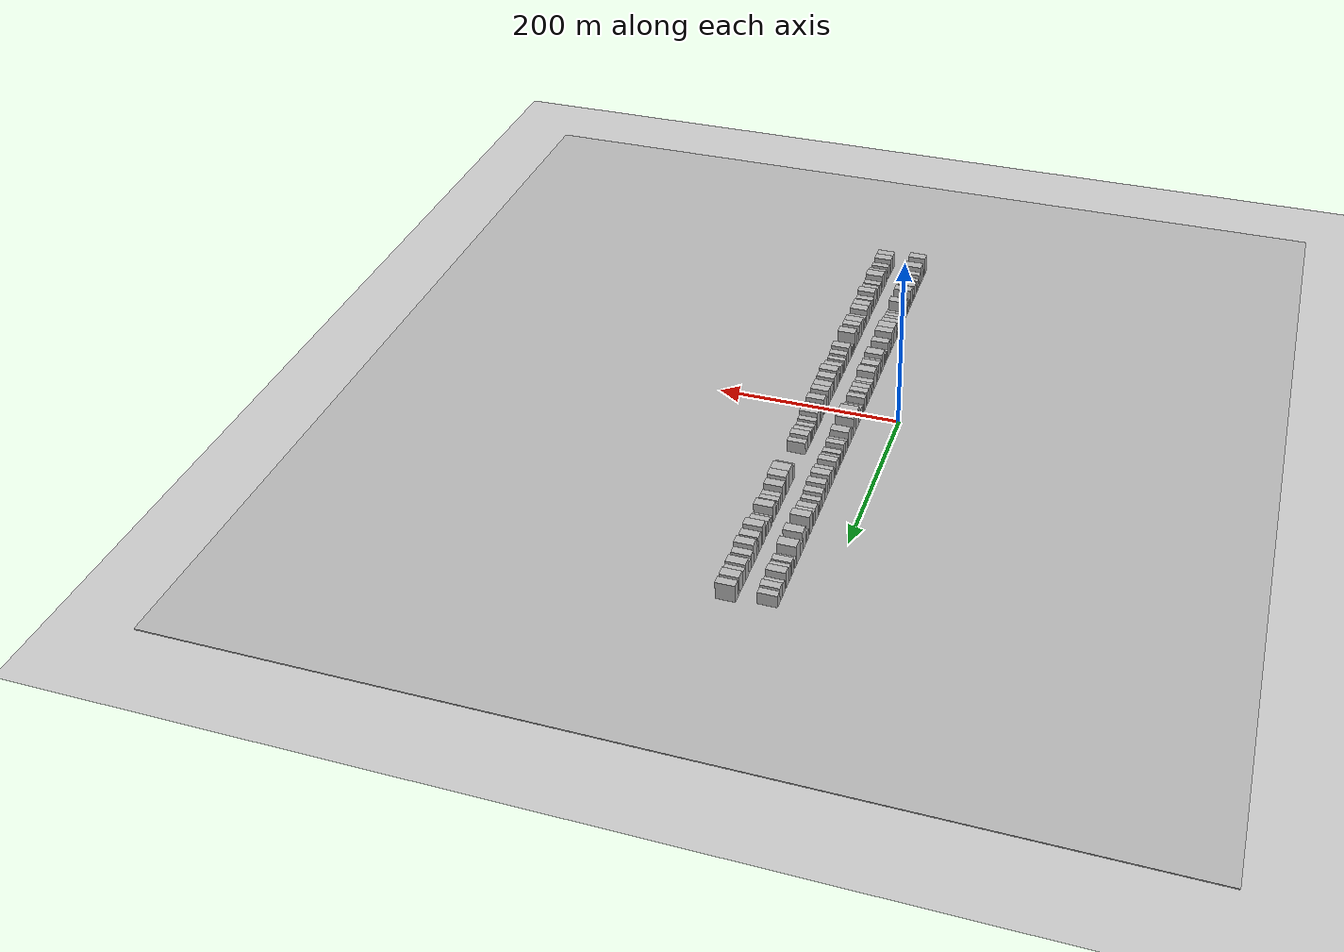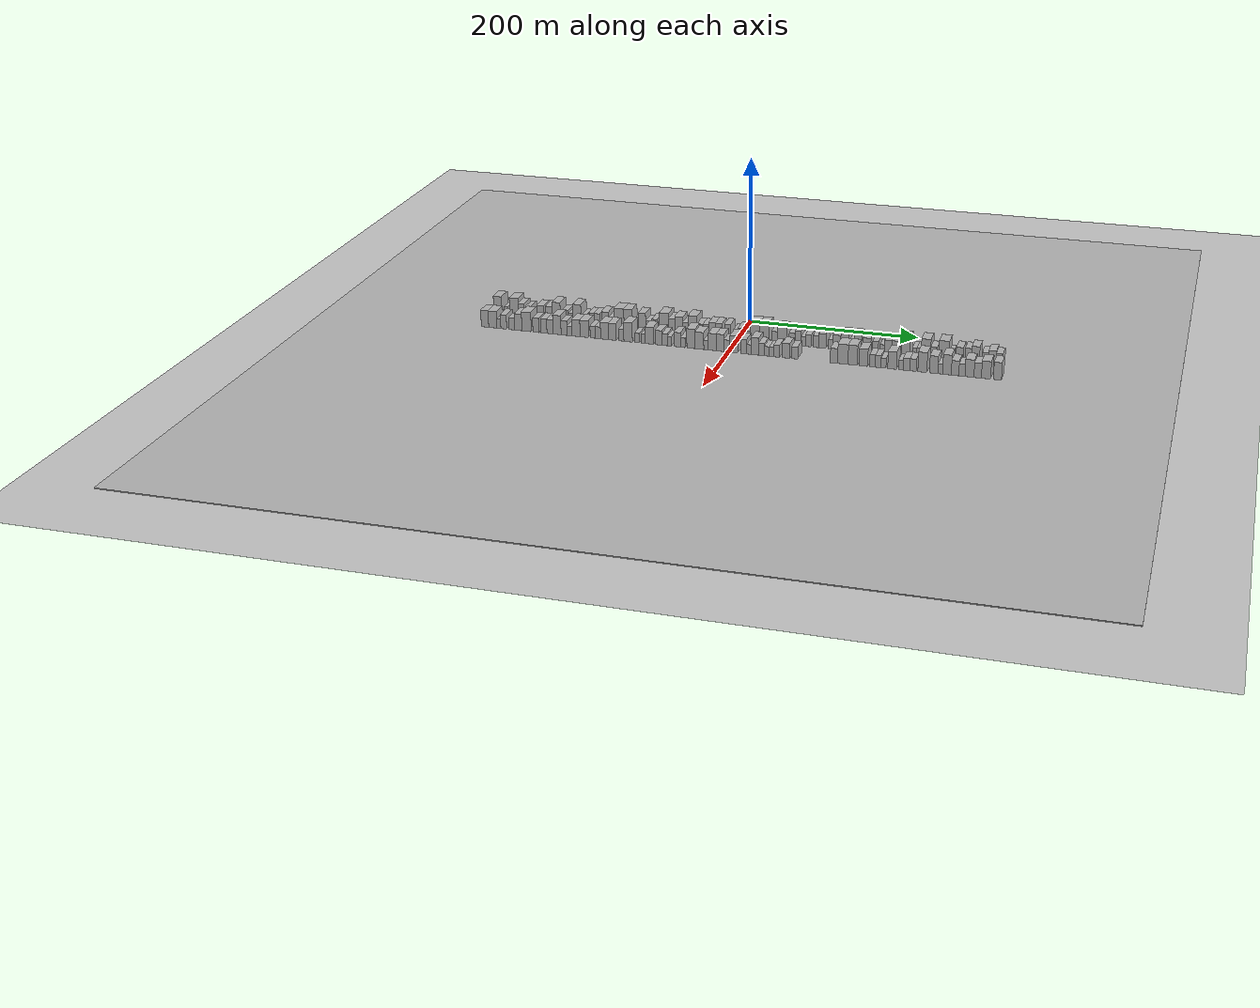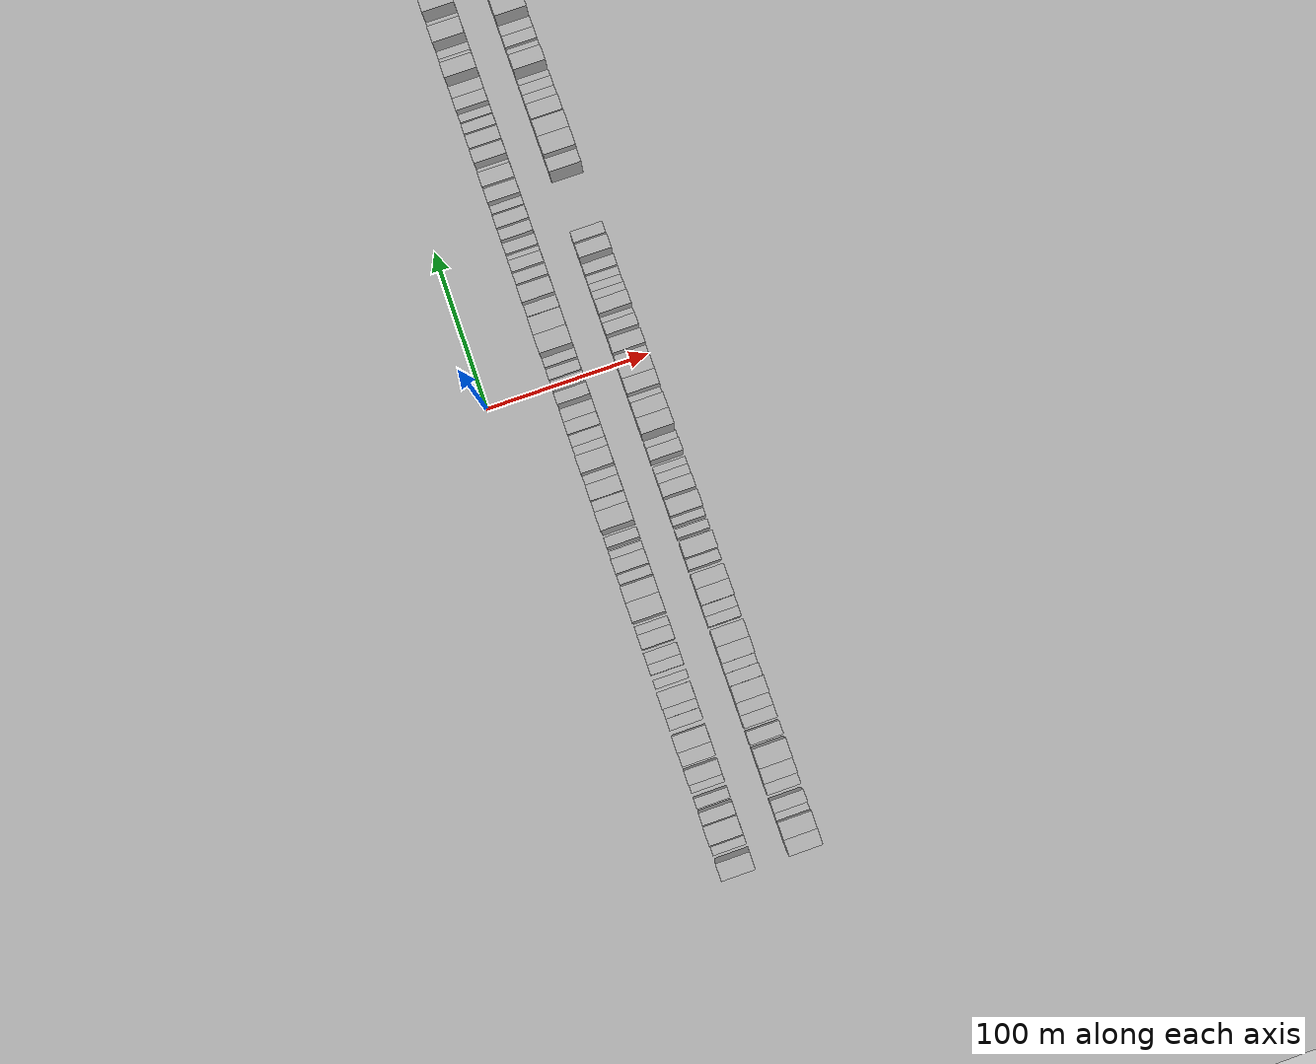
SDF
<?xml version="1.0" encoding="utf-8"?>

<sdf version="1.6">

   <world name="default">

      <gui fullscreen="0">

         <camera name="user_camera">

            <pose>-15 0 4.57585 0 0 0</pose>

            <view_controller>orbit</view_controller>

         </camera>

      </gui>

      <scene>

         <sky>

           <clouds>

             <speed>12</speed>

           </clouds>

         </sky>

         <ambient>0.4 0.4 0.4 1</ambient>

         <background>0.7 0.7 0.7 1</background>

         <shadows>1</shadows>

      </scene>

      <gravity>0 0 -9.8066</gravity>

      <magnetic_field>6e-06 2.3e-05 -4.2e-05</magnetic_field>

      <physics default="0" name="default_physics" type="ode">

         <ode>

            <solver>

               <type>quick</type>

               <iters>10</iters>

               <sor>1.0</sor>

               <use_dynamic_moi_rescaling>0</use_dynamic_moi_rescaling>

            </solver>

            <constraints>

               <cfm>0</cfm>

               <erp>0.2</erp>

               <contact_max_correcting_vel>100</contact_max_correcting_vel>

               <contact_surface_layer>0.001</contact_surface_layer>

            </constraints>

         </ode>

         <max_step_size>0.004</max_step_size>

         <real_time_factor>1</real_time_factor>

         <real_time_update_rate>250</real_time_update_rate>

      </physics>

      <light name="sun" type="directional">

         <cast_shadows>1</cast_shadows>

         <pose>0 0 10 0 0 0</pose>

         <diffuse>0.8 0.8 0.8 1</diffuse>

         <specular>0.2 0.2 0.2 1</specular>

         <attenuation>

            <range>1000</range>

            <constant>0.9</constant>

            <linear>0.01</linear>

            <quadratic>0.001</quadratic>

         </attenuation>

         <direction>-0.5 0.1 -0.9</direction>

      </light>

      <include>

         <name>ground_plane_1</name>

         <uri>model://HANNAS_ground_plane</uri>

         <pose>0 0 0  0 0 0</pose>

      </include>

      <include>

         <name>ground_plane_2</name>

         <uri>model://HANNAS_ground_plane</uri>

         <pose>100 0 0  0 0 0</pose>

      </include>

      <model name="building_1">

         <static>1</static>

         <pose frame="">50.0000 -294.9108 0 0.000000 0.000000 0.000000</pose>

         <link name="link">

            <pose frame="">0 0 12.00 0 0 0</pose>

            <collision name="collision">

               <geometry>

                  <box>

                     <size>20.0000 10.1784 24.0000</size>

                  </box>

               </geometry>

               <max_contacts>10</max_contacts>

               <surface>

                  <contact>

                     <ode/>

                  </contact>

                  <bounce/>

                  <friction>

                     <torsional>

                        <ode/>

                     </torsional>

                     <ode/>

                  </friction>

               </surface>

            </collision>

            <visual name="visual">

               <cast_shadows>0</cast_shadows>

               <geometry>

                  <box>

                     <size>20.0000 10.1784 24.0000</size>

                  </box>

               </geometry>

               <material>

                  <script>

                     <uri>model://HANNAS_wall/materials/scripts</uri>

                     <uri>model://HANNAS_wall/materials/textures</uri>

                     <name>vrc/HANNAS_wall</name>

                  </script>

               </material>

            </visual>

            <self_collide>0</self_collide>

            <enable_wind>0</enable_wind>

            <kinematic>0</kinematic>

         </link>

      </model>

      <model name="building_2">

         <static>1</static>

         <pose frame="">50.0000 -284.3145 0 0.000000 0.000000 0.000000</pose>

         <link name="link">

            <pose frame="">0 0 6.00 0 0 0</pose>

            <collision name="collision">

               <geometry>

                  <box>

                     <size>20.0000 5.0142 12.0000</size>

                  </box>

               </geometry>

               <max_contacts>10</max_contacts>

               <surface>

                  <contact>

                     <ode/>

                  </contact>

                  <bounce/>

                  <friction>

                     <torsional>

                        <ode/>

                     </torsional>

                     <ode/>

                  </friction>

               </surface>

            </collision>

            <visual name="visual">

               <cast_shadows>0</cast_shadows>

               <geometry>

                  <box>

                     <size>20.0000 5.0142 12.0000</size>

                  </box>

               </geometry>

               <material>

                  <script>

                     <uri>model://HANNAS_wall/materials/scripts</uri>

                     <uri>model://HANNAS_wall/materials/textures</uri>

                     <name>vrc/HANNAS_wall</name>

                  </script>

               </material>

            </visual>

            <self_collide>0</self_collide>

            <enable_wind>0</enable_wind>

            <kinematic>0</kinematic>

         </link>

      </model>

      <model name="building_3">

         <static>1</static>

         <pose frame="">50.0000 -274.2825 0 0.000000 0.000000 0.000000</pose>

         <link name="link">

            <pose frame="">0 0 12.00 0 0 0</pose>

            <collision name="collision">

               <geometry>

                  <box>

                     <size>20.0000 11.0498 24.0000</size>

                  </box>

               </geometry>

               <max_contacts>10</max_contacts>

               <surface>

                  <contact>

                     <ode/>

                  </contact>

                  <bounce/>

                  <friction>

                     <torsional>

                        <ode/>

                     </torsional>

                     <ode/>

                  </friction>

               </surface>

            </collision>

            <visual name="visual">

               <cast_shadows>0</cast_shadows>

               <geometry>

                  <box>

                     <size>20.0000 11.0498 24.0000</size>

                  </box>

               </geometry>

               <material>

                  <script>

                     <uri>model://HANNAS_wall/materials/scripts</uri>

                     <uri>model://HANNAS_wall/materials/textures</uri>

                     <name>vrc/HANNAS_wall</name>

                  </script>

               </material>

            </visual>

            <self_collide>0</self_collide>

            <enable_wind>0</enable_wind>

            <kinematic>0</kinematic>

         </link>

      </model>

      <model name="building_4">

         <static>1</static>

         <pose frame="">50.0000 -265.0465 0 0.000000 0.000000 0.000000</pose>

         <link name="link">

            <pose frame="">0 0 9.00 0 0 0</pose>

            <collision name="collision">

               <geometry>

                  <box>

                     <size>20.0000 7.4221 18.0000</size>

                  </box>

               </geometry>

               <max_contacts>10</max_contacts>

               <surface>

                  <contact>

                     <ode/>

                  </contact>

                  <bounce/>

                  <friction>

                     <torsional>

                        <ode/>

                     </torsional>

                     <ode/>

                  </friction>

               </surface>

            </collision>

            <visual name="visual">

               <cast_shadows>0</cast_shadows>

               <geometry>

                  <box>

                     <size>20.0000 7.4221 18.0000</size>

                  </box>

               </geometry>

               <material>

                  <script>

                     <uri>model://HANNAS_wall/materials/scripts</uri>

                     <uri>model://HANNAS_wall/materials/textures</uri>

                     <name>vrc/HANNAS_wall</name>

                  </script>

               </material>

            </visual>

            <self_collide>0</self_collide>

            <enable_wind>0</enable_wind>

            <kinematic>0</kinematic>

         </link>

      </model>

      <model name="building_5">

         <static>1</static>

         <pose frame="">50.0000 -256.2958 0 0.000000 0.000000 0.000000</pose>

         <link name="link">

            <pose frame="">0 0 7.50 0 0 0</pose>

            <collision name="collision">

               <geometry>

                  <box>

                     <size>20.0000 6.0794 15.0000</size>

                  </box>

               </geometry>

               <max_contacts>10</max_contacts>

               <surface>

                  <contact>

                     <ode/>

                  </contact>

                  <bounce/>

                  <friction>

                     <torsional>

                        <ode/>

                     </torsional>

                     <ode/>

                  </friction>

               </surface>

            </collision>

            <visual name="visual">

               <cast_shadows>0</cast_shadows>

               <geometry>

                  <box>

                     <size>20.0000 6.0794 15.0000</size>

                  </box>

               </geometry>

               <material>

                  <script>

                     <uri>model://HANNAS_wall/materials/scripts</uri>

                     <uri>model://HANNAS_wall/materials/textures</uri>

                     <name>vrc/HANNAS_wall</name>

                  </script>

               </material>

            </visual>

            <self_collide>0</self_collide>

            <enable_wind>0</enable_wind>

            <kinematic>0</kinematic>

         </link>

      </model>

      <model name="building_6">

         <static>1</static>

         <pose frame="">50.0000 -247.8401 0 0.000000 0.000000 0.000000</pose>

         <link name="link">

            <pose frame="">0 0 6.00 0 0 0</pose>

            <collision name="collision">

               <geometry>

                  <box>

                     <size>20.0000 4.8320 12.0000</size>

                  </box>

               </geometry>

               <max_contacts>10</max_contacts>

               <surface>

                  <contact>

                     <ode/>

                  </contact>

                  <bounce/>

                  <friction>

                     <torsional>

                        <ode/>

                     </torsional>

                     <ode/>

                  </friction>

               </surface>

            </collision>

            <visual name="visual">

               <cast_shadows>0</cast_shadows>

               <geometry>

                  <box>

                     <size>20.0000 4.8320 12.0000</size>

                  </box>

               </geometry>

               <material>

                  <script>

                     <uri>model://HANNAS_wall/materials/scripts</uri>

                     <uri>model://HANNAS_wall/materials/textures</uri>

                     <name>vrc/HANNAS_wall</name>

                  </script>

               </material>

            </visual>

            <self_collide>0</self_collide>

            <enable_wind>0</enable_wind>

            <kinematic>0</kinematic>

         </link>

      </model>

      <model name="building_7">

         <static>1</static>

         <pose frame="">50.0000 -240.9605 0 0.000000 0.000000 0.000000</pose>

         <link name="link">

            <pose frame="">0 0 9.00 0 0 0</pose>

            <collision name="collision">

               <geometry>

                  <box>

                     <size>20.0000 8.9272 18.0000</size>

                  </box>

               </geometry>

               <max_contacts>10</max_contacts>

               <surface>

                  <contact>

                     <ode/>

                  </contact>

                  <bounce/>

                  <friction>

                     <torsional>

                        <ode/>

                     </torsional>

                     <ode/>

                  </friction>

               </surface>

            </collision>

            <visual name="visual">

               <cast_shadows>0</cast_shadows>

               <geometry>

                  <box>

                     <size>20.0000 8.9272 18.0000</size>

                  </box>

               </geometry>

               <material>

                  <script>

                     <uri>model://HANNAS_wall/materials/scripts</uri>

                     <uri>model://HANNAS_wall/materials/textures</uri>

                     <name>vrc/HANNAS_wall</name>

                  </script>

               </material>

            </visual>

            <self_collide>0</self_collide>

            <enable_wind>0</enable_wind>

            <kinematic>0</kinematic>

         </link>

      </model>

      <model name="building_8">

         <static>1</static>

         <pose frame="">50.0000 -230.2648 0 0.000000 0.000000 0.000000</pose>

         <link name="link">

            <pose frame="">0 0 9.00 0 0 0</pose>

            <collision name="collision">

               <geometry>

                  <box>

                     <size>20.0000 8.4643 18.0000</size>

                  </box>

               </geometry>

               <max_contacts>10</max_contacts>

               <surface>

                  <contact>

                     <ode/>

                  </contact>

                  <bounce/>

                  <friction>

                     <torsional>

                        <ode/>

                     </torsional>

                     <ode/>

                  </friction>

               </surface>

            </collision>

            <visual name="visual">

               <cast_shadows>0</cast_shadows>

               <geometry>

                  <box>

                     <size>20.0000 8.4643 18.0000</size>

                  </box>

               </geometry>

               <material>

                  <script>

                     <uri>model://HANNAS_wall/materials/scripts</uri>

                     <uri>model://HANNAS_wall/materials/textures</uri>

                     <name>vrc/HANNAS_wall</name>

                  </script>

               </material>

            </visual>

            <self_collide>0</self_collide>

            <enable_wind>0</enable_wind>

            <kinematic>0</kinematic>

         </link>

      </model>

      <model name="building_9">

         <static>1</static>

         <pose frame="">50.0000 -221.1187 0 0.000000 0.000000 0.000000</pose>

         <link name="link">

            <pose frame="">0 0 12.00 0 0 0</pose>

            <collision name="collision">

               <geometry>

                  <box>

                     <size>20.0000 9.8279 24.0000</size>

                  </box>

               </geometry>

               <max_contacts>10</max_contacts>

               <surface>

                  <contact>

                     <ode/>

                  </contact>

                  <bounce/>

                  <friction>

                     <torsional>

                        <ode/>

                     </torsional>

                     <ode/>

                  </friction>

               </surface>

            </collision>

            <visual name="visual">

               <cast_shadows>0</cast_shadows>

               <geometry>

                  <box>

                     <size>20.0000 9.8279 24.0000</size>

                  </box>

               </geometry>

               <material>

                  <script>

                     <uri>model://HANNAS_wall/materials/scripts</uri>

                     <uri>model://HANNAS_wall/materials/textures</uri>

                     <name>vrc/HANNAS_wall</name>

                  </script>

               </material>

            </visual>

            <self_collide>0</self_collide>

            <enable_wind>0</enable_wind>

            <kinematic>0</kinematic>

         </link>

      </model>

      <model name="building_10">

         <static>1</static>

         <pose frame="">50.0000 -209.7433 0 0.000000 0.000000 0.000000</pose>

         <link name="link">

            <pose frame="">0 0 7.50 0 0 0</pose>

            <collision name="collision">

               <geometry>

                  <box>

                     <size>20.0000 6.9228 15.0000</size>

                  </box>

               </geometry>

               <max_contacts>10</max_contacts>

               <surface>

                  <contact>

                     <ode/>

                  </contact>

                  <bounce/>

                  <friction>

                     <torsional>

                        <ode/>

                     </torsional>

                     <ode/>

                  </friction>

               </surface>

            </collision>

            <visual name="visual">

               <cast_shadows>0</cast_shadows>

               <geometry>

                  <box>

                     <size>20.0000 6.9228 15.0000</size>

                  </box>

               </geometry>

               <material>

                  <script>

                     <uri>model://HANNAS_wall/materials/scripts</uri>

                     <uri>model://HANNAS_wall/materials/textures</uri>

                     <name>vrc/HANNAS_wall</name>

                  </script>

               </material>

            </visual>

            <self_collide>0</self_collide>

            <enable_wind>0</enable_wind>

            <kinematic>0</kinematic>

         </link>

      </model>

      <model name="building_11">

         <static>1</static>

         <pose frame="">50.0000 -203.3364 0 0.000000 0.000000 0.000000</pose>

         <link name="link">

            <pose frame="">0 0 6.00 0 0 0</pose>

            <collision name="collision">

               <geometry>

                  <box>

                     <size>20.0000 5.8911 12.0000</size>

                  </box>

               </geometry>

               <max_contacts>10</max_contacts>

               <surface>

                  <contact>

                     <ode/>

                  </contact>

                  <bounce/>

                  <friction>

                     <torsional>

                        <ode/>

                     </torsional>

                     <ode/>

                  </friction>

               </surface>

            </collision>

            <visual name="visual">

               <cast_shadows>0</cast_shadows>

               <geometry>

                  <box>

                     <size>20.0000 5.8911 12.0000</size>

                  </box>

               </geometry>

               <material>

                  <script>

                     <uri>model://HANNAS_wall/materials/scripts</uri>

                     <uri>model://HANNAS_wall/materials/textures</uri>

                     <name>vrc/HANNAS_wall</name>

                  </script>

               </material>

            </visual>

            <self_collide>0</self_collide>

            <enable_wind>0</enable_wind>

            <kinematic>0</kinematic>

         </link>

      </model>

      <model name="building_12">

         <static>1</static>

         <pose frame="">50.0000 -195.4304 0 0.000000 0.000000 0.000000</pose>

         <link name="link">

            <pose frame="">0 0 12.00 0 0 0</pose>

            <collision name="collision">

               <geometry>

                  <box>

                     <size>20.0000 9.9209 24.0000</size>

                  </box>

               </geometry>

               <max_contacts>10</max_contacts>

               <surface>

                  <contact>

                     <ode/>

                  </contact>

                  <bounce/>

                  <friction>

                     <torsional>

                        <ode/>

                     </torsional>

                     <ode/>

                  </friction>

               </surface>

            </collision>

            <visual name="visual">

               <cast_shadows>0</cast_shadows>

               <geometry>

                  <box>

                     <size>20.0000 9.9209 24.0000</size>

                  </box>

               </geometry>

               <material>

                  <script>

                     <uri>model://HANNAS_wall/materials/scripts</uri>

                     <uri>model://HANNAS_wall/materials/textures</uri>

                     <name>vrc/HANNAS_wall</name>

                  </script>

               </material>

            </visual>

            <self_collide>0</self_collide>

            <enable_wind>0</enable_wind>

            <kinematic>0</kinematic>

         </link>

      </model>

      <model name="building_13">

         <static>1</static>

         <pose frame="">50.0000 -185.8845 0 0.000000 0.000000 0.000000</pose>

         <link name="link">

            <pose frame="">0 0 6.00 0 0 0</pose>

            <collision name="collision">

               <geometry>

                  <box>

                     <size>20.0000 5.1708 12.0000</size>

                  </box>

               </geometry>

               <max_contacts>10</max_contacts>

               <surface>

                  <contact>

                     <ode/>

                  </contact>

                  <bounce/>

                  <friction>

                     <torsional>

                        <ode/>

                     </torsional>

                     <ode/>

                  </friction>

               </surface>

            </collision>

            <visual name="visual">

               <cast_shadows>0</cast_shadows>

               <geometry>

                  <box>

                     <size>20.0000 5.1708 12.0000</size>

                  </box>

               </geometry>

               <material>

                  <script>

                     <uri>model://HANNAS_wall/materials/scripts</uri>

                     <uri>model://HANNAS_wall/materials/textures</uri>

                     <name>vrc/HANNAS_wall</name>

                  </script>

               </material>

            </visual>

            <self_collide>0</self_collide>

            <enable_wind>0</enable_wind>

            <kinematic>0</kinematic>

         </link>

      </model>

      <model name="building_14">

         <static>1</static>

         <pose frame="">50.0000 -177.2274 0 0.000000 0.000000 0.000000</pose>

         <link name="link">

            <pose frame="">0 0 7.50 0 0 0</pose>

            <collision name="collision">

               <geometry>

                  <box>

                     <size>20.0000 6.1435 15.0000</size>

                  </box>

               </geometry>

               <max_contacts>10</max_contacts>

               <surface>

                  <contact>

                     <ode/>

                  </contact>

                  <bounce/>

                  <friction>

                     <torsional>

                        <ode/>

                     </torsional>

                     <ode/>

                  </friction>

               </surface>

            </collision>

            <visual name="visual">

               <cast_shadows>0</cast_shadows>

               <geometry>

                  <box>

                     <size>20.0000 6.1435 15.0000</size>

                  </box>

               </geometry>

               <material>

                  <script>

                     <uri>model://HANNAS_wall/materials/scripts</uri>

                     <uri>model://HANNAS_wall/materials/textures</uri>

                     <name>vrc/HANNAS_wall</name>

                  </script>

               </material>

            </visual>

            <self_collide>0</self_collide>

            <enable_wind>0</enable_wind>

            <kinematic>0</kinematic>

         </link>

      </model>

      <model name="building_15">

         <static>1</static>

         <pose frame="">50.0000 -170.5829 0 0.000000 0.000000 0.000000</pose>

         <link name="link">

            <pose frame="">0 0 7.50 0 0 0</pose>

            <collision name="collision">

               <geometry>

                  <box>

                     <size>20.0000 7.1455 15.0000</size>

                  </box>

               </geometry>

               <max_contacts>10</max_contacts>

               <surface>

                  <contact>

                     <ode/>

                  </contact>

                  <bounce/>

                  <friction>

                     <torsional>

                        <ode/>

                     </torsional>

                     <ode/>

                  </friction>

               </surface>

            </collision>

            <visual name="visual">

               <cast_shadows>0</cast_shadows>

               <geometry>

                  <box>

                     <size>20.0000 7.1455 15.0000</size>

                  </box>

               </geometry>

               <material>

                  <script>

                     <uri>model://HANNAS_wall/materials/scripts</uri>

                     <uri>model://HANNAS_wall/materials/textures</uri>

                     <name>vrc/HANNAS_wall</name>

                  </script>

               </material>

            </visual>

            <self_collide>0</self_collide>

            <enable_wind>0</enable_wind>

            <kinematic>0</kinematic>

         </link>

      </model>

      <model name="building_16">

         <static>1</static>

         <pose frame="">50.0000 -160.6937 0 0.000000 0.000000 0.000000</pose>

         <link name="link">

            <pose frame="">0 0 9.00 0 0 0</pose>

            <collision name="collision">

               <geometry>

                  <box>

                     <size>20.0000 8.6328 18.0000</size>

                  </box>

               </geometry>

               <max_contacts>10</max_contacts>

               <surface>

                  <contact>

                     <ode/>

                  </contact>

                  <bounce/>

                  <friction>

                     <torsional>

                        <ode/>

                     </torsional>

                     <ode/>

                  </friction>

               </surface>

            </collision>

            <visual name="visual">

               <cast_shadows>0</cast_shadows>

               <geometry>

                  <box>

                     <size>20.0000 8.6328 18.0000</size>

                  </box>

               </geometry>

               <material>

                  <script>

                     <uri>model://HANNAS_wall/materials/scripts</uri>

                     <uri>model://HANNAS_wall/materials/textures</uri>

                     <name>vrc/HANNAS_wall</name>

                  </script>

               </material>

            </visual>

            <self_collide>0</self_collide>

            <enable_wind>0</enable_wind>

            <kinematic>0</kinematic>

         </link>

      </model>

      <model name="building_17">

         <static>1</static>

         <pose frame="">50.0000 -153.6714 0 0.000000 0.000000 0.000000</pose>

         <link name="link">

            <pose frame="">0 0 6.00 0 0 0</pose>

            <collision name="collision">

               <geometry>

                  <box>

                     <size>20.0000 5.4120 12.0000</size>

                  </box>

               </geometry>

               <max_contacts>10</max_contacts>

               <surface>

                  <contact>

                     <ode/>

                  </contact>

                  <bounce/>

                  <friction>

                     <torsional>

                        <ode/>

                     </torsional>

                     <ode/>

                  </friction>

               </surface>

            </collision>

            <visual name="visual">

               <cast_shadows>0</cast_shadows>

               <geometry>

                  <box>

                     <size>20.0000 5.4120 12.0000</size>

                  </box>

               </geometry>

               <material>

                  <script>

                     <uri>model://HANNAS_wall/materials/scripts</uri>

                     <uri>model://HANNAS_wall/materials/textures</uri>

                     <name>vrc/HANNAS_wall</name>

                  </script>

               </material>

            </visual>

            <self_collide>0</self_collide>

            <enable_wind>0</enable_wind>

            <kinematic>0</kinematic>

         </link>

      </model>

      <model name="building_18">

         <static>1</static>

         <pose frame="">50.0000 -143.1797 0 0.000000 0.000000 0.000000</pose>

         <link name="link">

            <pose frame="">0 0 12.00 0 0 0</pose>

            <collision name="collision">

               <geometry>

                  <box>

                     <size>20.0000 11.5714 24.0000</size>

                  </box>

               </geometry>

               <max_contacts>10</max_contacts>

               <surface>

                  <contact>

                     <ode/>

                  </contact>

                  <bounce/>

                  <friction>

                     <torsional>

                        <ode/>

                     </torsional>

                     <ode/>

                  </friction>

               </surface>

            </collision>

            <visual name="visual">

               <cast_shadows>0</cast_shadows>

               <geometry>

                  <box>

                     <size>20.0000 11.5714 24.0000</size>

                  </box>

               </geometry>

               <material>

                  <script>

                     <uri>model://HANNAS_wall/materials/scripts</uri>

                     <uri>model://HANNAS_wall/materials/textures</uri>

                     <name>vrc/HANNAS_wall</name>

                  </script>

               </material>

            </visual>

            <self_collide>0</self_collide>

            <enable_wind>0</enable_wind>

            <kinematic>0</kinematic>

         </link>

      </model>

      <model name="building_19">

         <static>1</static>

         <pose frame="">50.0000 -132.5070 0 0.000000 0.000000 0.000000</pose>

         <link name="link">

            <pose frame="">0 0 12.00 0 0 0</pose>

            <collision name="collision">

               <geometry>

                  <box>

                     <size>20.0000 9.7740 24.0000</size>

                  </box>

               </geometry>

               <max_contacts>10</max_contacts>

               <surface>

                  <contact>

                     <ode/>

                  </contact>

                  <bounce/>

                  <friction>

                     <torsional>

                        <ode/>

                     </torsional>

                     <ode/>

                  </friction>

               </surface>

            </collision>

            <visual name="visual">

               <cast_shadows>0</cast_shadows>

               <geometry>

                  <box>

                     <size>20.0000 9.7740 24.0000</size>

                  </box>

               </geometry>

               <material>

                  <script>

                     <uri>model://HANNAS_wall/materials/scripts</uri>

                     <uri>model://HANNAS_wall/materials/textures</uri>

                     <name>vrc/HANNAS_wall</name>

                  </script>

               </material>

            </visual>

            <self_collide>0</self_collide>

            <enable_wind>0</enable_wind>

            <kinematic>0</kinematic>

         </link>

      </model>

      <model name="building_20">

         <static>1</static>

         <pose frame="">50.0000 -122.6663 0 0.000000 0.000000 0.000000</pose>

         <link name="link">

            <pose frame="">0 0 6.00 0 0 0</pose>

            <collision name="collision">

               <geometry>

                  <box>

                     <size>20.0000 5.9075 12.0000</size>

                  </box>

               </geometry>

               <max_contacts>10</max_contacts>

               <surface>

                  <contact>

                     <ode/>

                  </contact>

                  <bounce/>

                  <friction>

                     <torsional>

                        <ode/>

                     </torsional>

                     <ode/>

                  </friction>

               </surface>

            </collision>

            <visual name="visual">

               <cast_shadows>0</cast_shadows>

               <geometry>

                  <box>

                     <size>20.0000 5.9075 12.0000</size>

                  </box>

               </geometry>

               <material>

                  <script>

                     <uri>model://HANNAS_wall/materials/scripts</uri>

                     <uri>model://HANNAS_wall/materials/textures</uri>

                     <name>vrc/HANNAS_wall</name>

                  </script>

               </material>

            </visual>

            <self_collide>0</self_collide>

            <enable_wind>0</enable_wind>

            <kinematic>0</kinematic>

         </link>

      </model>

      <model name="building_21">

         <static>1</static>

         <pose frame="">50.0000 -115.2977 0 0.000000 0.000000 0.000000</pose>

         <link name="link">

            <pose frame="">0 0 10.50 0 0 0</pose>

            <collision name="collision">

               <geometry>

                  <box>

                     <size>20.0000 8.8297 21.0000</size>

                  </box>

               </geometry>

               <max_contacts>10</max_contacts>

               <surface>

                  <contact>

                     <ode/>

                  </contact>

                  <bounce/>

                  <friction>

                     <torsional>

                        <ode/>

                     </torsional>

                     <ode/>

                  </friction>

               </surface>

            </collision>

            <visual name="visual">

               <cast_shadows>0</cast_shadows>

               <geometry>

                  <box>

                     <size>20.0000 8.8297 21.0000</size>

                  </box>

               </geometry>

               <material>

                  <script>

                     <uri>model://HANNAS_wall/materials/scripts</uri>

                     <uri>model://HANNAS_wall/materials/textures</uri>

                     <name>vrc/HANNAS_wall</name>

                  </script>

               </material>

            </visual>

            <self_collide>0</self_collide>

            <enable_wind>0</enable_wind>

            <kinematic>0</kinematic>

         </link>

      </model>

      <model name="building_22">

         <static>1</static>

         <pose frame="">50.0000 -108.0368 0 0.000000 0.000000 0.000000</pose>

         <link name="link">

            <pose frame="">0 0 6.00 0 0 0</pose>

            <collision name="collision">

               <geometry>

                  <box>

                     <size>20.0000 5.6920 12.0000</size>

                  </box>

               </geometry>

               <max_contacts>10</max_contacts>

               <surface>

                  <contact>

                     <ode/>

                  </contact>

                  <bounce/>

                  <friction>

                     <torsional>

                        <ode/>

                     </torsional>

                     <ode/>

                  </friction>

               </surface>

            </collision>

            <visual name="visual">

               <cast_shadows>0</cast_shadows>

               <geometry>

                  <box>

                     <size>20.0000 5.6920 12.0000</size>

                  </box>

               </geometry>

               <material>

                  <script>

                     <uri>model://HANNAS_wall/materials/scripts</uri>

                     <uri>model://HANNAS_wall/materials/textures</uri>

                     <name>vrc/HANNAS_wall</name>

                  </script>

               </material>

            </visual>

            <self_collide>0</self_collide>

            <enable_wind>0</enable_wind>

            <kinematic>0</kinematic>

         </link>

      </model>

      <model name="building_23">

         <static>1</static>

         <pose frame="">50.0000 -100.0813 0 0.000000 0.000000 0.000000</pose>

         <link name="link">

            <pose frame="">0 0 7.50 0 0 0</pose>

            <collision name="collision">

               <geometry>

                  <box>

                     <size>20.0000 6.2189 15.0000</size>

                  </box>

               </geometry>

               <max_contacts>10</max_contacts>

               <surface>

                  <contact>

                     <ode/>

                  </contact>

                  <bounce/>

                  <friction>

                     <torsional>

                        <ode/>

                     </torsional>

                     <ode/>

                  </friction>

               </surface>

            </collision>

            <visual name="visual">

               <cast_shadows>0</cast_shadows>

               <geometry>

                  <box>

                     <size>20.0000 6.2189 15.0000</size>

                  </box>

               </geometry>

               <material>

                  <script>

                     <uri>model://HANNAS_wall/materials/scripts</uri>

                     <uri>model://HANNAS_wall/materials/textures</uri>

                     <name>vrc/HANNAS_wall</name>

                  </script>

               </material>

            </visual>

            <self_collide>0</self_collide>

            <enable_wind>0</enable_wind>

            <kinematic>0</kinematic>

         </link>

      </model>

      <model name="building_24">

         <static>1</static>

         <pose frame="">50.0000 -88.3045 0 0.000000 0.000000 0.000000</pose>

         <link name="link">

            <pose frame="">0 0 12.00 0 0 0</pose>

            <collision name="collision">

               <geometry>

                  <box>

                     <size>20.0000 11.3347 24.0000</size>

                  </box>

               </geometry>

               <max_contacts>10</max_contacts>

               <surface>

                  <contact>

                     <ode/>

                  </contact>

                  <bounce/>

                  <friction>

                     <torsional>

                        <ode/>

                     </torsional>

                     <ode/>

                  </friction>

               </surface>

            </collision>

            <visual name="visual">

               <cast_shadows>0</cast_shadows>

               <geometry>

                  <box>

                     <size>20.0000 11.3347 24.0000</size>

                  </box>

               </geometry>

               <material>

                  <script>

                     <uri>model://HANNAS_wall/materials/scripts</uri>

                     <uri>model://HANNAS_wall/materials/textures</uri>

                     <name>vrc/HANNAS_wall</name>

                  </script>

               </material>

            </visual>

            <self_collide>0</self_collide>

            <enable_wind>0</enable_wind>

            <kinematic>0</kinematic>

         </link>

      </model>

      <model name="building_25">

         <static>1</static>

         <pose frame="">50.0000 -79.0158 0 0.000000 0.000000 0.000000</pose>

         <link name="link">

            <pose frame="">0 0 9.00 0 0 0</pose>

            <collision name="collision">

               <geometry>

                  <box>

                     <size>20.0000 7.2427 18.0000</size>

                  </box>

               </geometry>

               <max_contacts>10</max_contacts>

               <surface>

                  <contact>

                     <ode/>

                  </contact>

                  <bounce/>

                  <friction>

                     <torsional>

                        <ode/>

                     </torsional>

                     <ode/>

                  </friction>

               </surface>

            </collision>

            <visual name="visual">

               <cast_shadows>0</cast_shadows>

               <geometry>

                  <box>

                     <size>20.0000 7.2427 18.0000</size>

                  </box>

               </geometry>

               <material>

                  <script>

                     <uri>model://HANNAS_wall/materials/scripts</uri>

                     <uri>model://HANNAS_wall/materials/textures</uri>

                     <name>vrc/HANNAS_wall</name>

                  </script>

               </material>

            </visual>

            <self_collide>0</self_collide>

            <enable_wind>0</enable_wind>

            <kinematic>0</kinematic>

         </link>

      </model>

      <model name="building_26">

         <static>1</static>

         <pose frame="">50.0000 -70.5292 0 0.000000 0.000000 0.000000</pose>

         <link name="link">

            <pose frame="">0 0 10.50 0 0 0</pose>

            <collision name="collision">

               <geometry>

                  <box>

                     <size>20.0000 9.7304 21.0000</size>

                  </box>

               </geometry>

               <max_contacts>10</max_contacts>

               <surface>

                  <contact>

                     <ode/>

                  </contact>

                  <bounce/>

                  <friction>

                     <torsional>

                        <ode/>

                     </torsional>

                     <ode/>

                  </friction>

               </surface>

            </collision>

            <visual name="visual">

               <cast_shadows>0</cast_shadows>

               <geometry>

                  <box>

                     <size>20.0000 9.7304 21.0000</size>

                  </box>

               </geometry>

               <material>

                  <script>

                     <uri>model://HANNAS_wall/materials/scripts</uri>

                     <uri>model://HANNAS_wall/materials/textures</uri>

                     <name>vrc/HANNAS_wall</name>

                  </script>

               </material>

            </visual>

            <self_collide>0</self_collide>

            <enable_wind>0</enable_wind>

            <kinematic>0</kinematic>

         </link>

      </model>

      <model name="building_27">

         <static>1</static>

         <pose frame="">50.0000 -62.3960 0 0.000000 0.000000 0.000000</pose>

         <link name="link">

            <pose frame="">0 0 7.50 0 0 0</pose>

            <collision name="collision">

               <geometry>

                  <box>

                     <size>20.0000 6.5360 15.0000</size>

                  </box>

               </geometry>

               <max_contacts>10</max_contacts>

               <surface>

                  <contact>

                     <ode/>

                  </contact>

                  <bounce/>

                  <friction>

                     <torsional>

                        <ode/>

                     </torsional>

                     <ode/>

                  </friction>

               </surface>

            </collision>

            <visual name="visual">

               <cast_shadows>0</cast_shadows>

               <geometry>

                  <box>

                     <size>20.0000 6.5360 15.0000</size>

                  </box>

               </geometry>

               <material>

                  <script>

                     <uri>model://HANNAS_wall/materials/scripts</uri>

                     <uri>model://HANNAS_wall/materials/textures</uri>

                     <name>vrc/HANNAS_wall</name>

                  </script>

               </material>

            </visual>

            <self_collide>0</self_collide>

            <enable_wind>0</enable_wind>

            <kinematic>0</kinematic>

         </link>

      </model>

      <model name="building_28">

         <static>1</static>

         <pose frame="">50.0000 -53.7417 0 0.000000 0.000000 0.000000</pose>

         <link name="link">

            <pose frame="">0 0 12.00 0 0 0</pose>

            <collision name="collision">

               <geometry>

                  <box>

                     <size>20.0000 10.7727 24.0000</size>

                  </box>

               </geometry>

               <max_contacts>10</max_contacts>

               <surface>

                  <contact>

                     <ode/>

                  </contact>

                  <bounce/>

                  <friction>

                     <torsional>

                        <ode/>

                     </torsional>

                     <ode/>

                  </friction>

               </surface>

            </collision>

            <visual name="visual">

               <cast_shadows>0</cast_shadows>

               <geometry>

                  <box>

                     <size>20.0000 10.7727 24.0000</size>

                  </box>

               </geometry>

               <material>

                  <script>

                     <uri>model://HANNAS_wall/materials/scripts</uri>

                     <uri>model://HANNAS_wall/materials/textures</uri>

                     <name>vrc/HANNAS_wall</name>

                  </script>

               </material>

            </visual>

            <self_collide>0</self_collide>

            <enable_wind>0</enable_wind>

            <kinematic>0</kinematic>

         </link>

      </model>

      <model name="building_29">

         <static>1</static>

         <pose frame="">50.0000 -44.8330 0 0.000000 0.000000 0.000000</pose>

         <link name="link">

            <pose frame="">0 0 7.50 0 0 0</pose>

            <collision name="collision">

               <geometry>

                  <box>

                     <size>20.0000 7.0446 15.0000</size>

                  </box>

               </geometry>

               <max_contacts>10</max_contacts>

               <surface>

                  <contact>

                     <ode/>

                  </contact>

                  <bounce/>

                  <friction>

                     <torsional>

                        <ode/>

                     </torsional>

                     <ode/>

                  </friction>

               </surface>

            </collision>

            <visual name="visual">

               <cast_shadows>0</cast_shadows>

               <geometry>

                  <box>

                     <size>20.0000 7.0446 15.0000</size>

                  </box>

               </geometry>

               <material>

                  <script>

                     <uri>model://HANNAS_wall/materials/scripts</uri>

                     <uri>model://HANNAS_wall/materials/textures</uri>

                     <name>vrc/HANNAS_wall</name>

                  </script>

               </material>

            </visual>

            <self_collide>0</self_collide>

            <enable_wind>0</enable_wind>

            <kinematic>0</kinematic>

         </link>

      </model>

      <model name="building_30">

         <static>1</static>

         <pose frame="">50.0000 -37.7096 0 0.000000 0.000000 0.000000</pose>

         <link name="link">

            <pose frame="">0 0 7.50 0 0 0</pose>

            <collision name="collision">

               <geometry>

                  <box>

                     <size>20.0000 7.2022 15.0000</size>

                  </box>

               </geometry>

               <max_contacts>10</max_contacts>

               <surface>

                  <contact>

                     <ode/>

                  </contact>

                  <bounce/>

                  <friction>

                     <torsional>

                        <ode/>

                     </torsional>

                     <ode/>

                  </friction>

               </surface>

            </collision>

            <visual name="visual">

               <cast_shadows>0</cast_shadows>

               <geometry>

                  <box>

                     <size>20.0000 7.2022 15.0000</size>

                  </box>

               </geometry>

               <material>

                  <script>

                     <uri>model://HANNAS_wall/materials/scripts</uri>

                     <uri>model://HANNAS_wall/materials/textures</uri>

                     <name>vrc/HANNAS_wall</name>

                  </script>

               </material>

            </visual>

            <self_collide>0</self_collide>

            <enable_wind>0</enable_wind>

            <kinematic>0</kinematic>

         </link>

      </model>

      <model name="building_31">

         <static>1</static>

         <pose frame="">50.0000 -30.2062 0 0.000000 0.000000 0.000000</pose>

         <link name="link">

            <pose frame="">0 0 9.00 0 0 0</pose>

            <collision name="collision">

               <geometry>

                  <box>

                     <size>20.0000 7.8048 18.0000</size>

                  </box>

               </geometry>

               <max_contacts>10</max_contacts>

               <surface>

                  <contact>

                     <ode/>

                  </contact>

                  <bounce/>

                  <friction>

                     <torsional>

                        <ode/>

                     </torsional>

                     <ode/>

                  </friction>

               </surface>

            </collision>

            <visual name="visual">

               <cast_shadows>0</cast_shadows>

               <geometry>

                  <box>

                     <size>20.0000 7.8048 18.0000</size>

                  </box>

               </geometry>

               <material>

                  <script>

                     <uri>model://HANNAS_wall/materials/scripts</uri>

                     <uri>model://HANNAS_wall/materials/textures</uri>

                     <name>vrc/HANNAS_wall</name>

                  </script>

               </material>

            </visual>

            <self_collide>0</self_collide>

            <enable_wind>0</enable_wind>

            <kinematic>0</kinematic>

         </link>

      </model>

      <model name="building_32">

         <static>1</static>

         <pose frame="">50.0000 -22.3476 0 0.000000 0.000000 0.000000</pose>

         <link name="link">

            <pose frame="">0 0 9.00 0 0 0</pose>

            <collision name="collision">

               <geometry>

                  <box>

                     <size>20.0000 7.9123 18.0000</size>

                  </box>

               </geometry>

               <max_contacts>10</max_contacts>

               <surface>

                  <contact>

                     <ode/>

                  </contact>

                  <bounce/>

                  <friction>

                     <torsional>

                        <ode/>

                     </torsional>

                     <ode/>

                  </friction>

               </surface>

            </collision>

            <visual name="visual">

               <cast_shadows>0</cast_shadows>

               <geometry>

                  <box>

                     <size>20.0000 7.9123 18.0000</size>

                  </box>

               </geometry>

               <material>

                  <script>

                     <uri>model://HANNAS_wall/materials/scripts</uri>

                     <uri>model://HANNAS_wall/materials/textures</uri>

                     <name>vrc/HANNAS_wall</name>

                  </script>

               </material>

            </visual>

            <self_collide>0</self_collide>

            <enable_wind>0</enable_wind>

            <kinematic>0</kinematic>

         </link>

      </model>

      <model name="building_33">

         <static>1</static>

         <pose frame="">50.0000 -11.7090 0 0.000000 0.000000 0.000000</pose>

         <link name="link">

            <pose frame="">0 0 9.00 0 0 0</pose>

            <collision name="collision">

               <geometry>

                  <box>

                     <size>20.0000 7.3649 18.0000</size>

                  </box>

               </geometry>

               <max_contacts>10</max_contacts>

               <surface>

                  <contact>

                     <ode/>

                  </contact>

                  <bounce/>

                  <friction>

                     <torsional>

                        <ode/>

                     </torsional>

                     <ode/>

                  </friction>

               </surface>

            </collision>

            <visual name="visual">

               <cast_shadows>0</cast_shadows>

               <geometry>

                  <box>

                     <size>20.0000 7.3649 18.0000</size>

                  </box>

               </geometry>

               <material>

                  <script>

                     <uri>model://HANNAS_wall/materials/scripts</uri>

                     <uri>model://HANNAS_wall/materials/textures</uri>

                     <name>vrc/HANNAS_wall</name>

                  </script>

               </material>

            </visual>

            <self_collide>0</self_collide>

            <enable_wind>0</enable_wind>

            <kinematic>0</kinematic>

         </link>

      </model>

      <model name="building_34">

         <static>1</static>

         <pose frame="">50.0000 -2.1752 0 0.000000 0.000000 0.000000</pose>

         <link name="link">

            <pose frame="">0 0 6.00 0 0 0</pose>

            <collision name="collision">

               <geometry>

                  <box>

                     <size>20.0000 5.7027 12.0000</size>

                  </box>

               </geometry>

               <max_contacts>10</max_contacts>

               <surface>

                  <contact>

                     <ode/>

                  </contact>

                  <bounce/>

                  <friction>

                     <torsional>

                        <ode/>

                     </torsional>

                     <ode/>

                  </friction>

               </surface>

            </collision>

            <visual name="visual">

               <cast_shadows>0</cast_shadows>

               <geometry>

                  <box>

                     <size>20.0000 5.7027 12.0000</size>

                  </box>

               </geometry>

               <material>

                  <script>

                     <uri>model://HANNAS_wall/materials/scripts</uri>

                     <uri>model://HANNAS_wall/materials/textures</uri>

                     <name>vrc/HANNAS_wall</name>

                  </script>

               </material>

            </visual>

            <self_collide>0</self_collide>

            <enable_wind>0</enable_wind>

            <kinematic>0</kinematic>

         </link>

      </model>

      <model name="building_35">

         <static>1</static>

         <pose frame="">50.0000 3.9535 0 0.000000 0.000000 0.000000</pose>

         <link name="link">

            <pose frame="">0 0 7.50 0 0 0</pose>

            <collision name="collision">

               <geometry>

                  <box>

                     <size>20.0000 6.5547 15.0000</size>

                  </box>

               </geometry>

               <max_contacts>10</max_contacts>

               <surface>

                  <contact>

                     <ode/>

                  </contact>

                  <bounce/>

                  <friction>

                     <torsional>

                        <ode/>

                     </torsional>

                     <ode/>

                  </friction>

               </surface>

            </collision>

            <visual name="visual">

               <cast_shadows>0</cast_shadows>

               <geometry>

                  <box>

                     <size>20.0000 6.5547 15.0000</size>

                  </box>

               </geometry>

               <material>

                  <script>

                     <uri>model://HANNAS_wall/materials/scripts</uri>

                     <uri>model://HANNAS_wall/materials/textures</uri>

                     <name>vrc/HANNAS_wall</name>

                  </script>

               </material>

            </visual>

            <self_collide>0</self_collide>

            <enable_wind>0</enable_wind>

            <kinematic>0</kinematic>

         </link>

      </model>

      <model name="building_36">

         <static>1</static>

         <pose frame="">50.0000 12.1272 0 0.000000 0.000000 0.000000</pose>

         <link name="link">

            <pose frame="">0 0 6.00 0 0 0</pose>

            <collision name="collision">

               <geometry>

                  <box>

                     <size>20.0000 5.7927 12.0000</size>

                  </box>

               </geometry>

               <max_contacts>10</max_contacts>

               <surface>

                  <contact>

                     <ode/>

                  </contact>

                  <bounce/>

                  <friction>

                     <torsional>

                        <ode/>

                     </torsional>

                     <ode/>

                  </friction>

               </surface>

            </collision>

            <visual name="visual">

               <cast_shadows>0</cast_shadows>

               <geometry>

                  <box>

                     <size>20.0000 5.7927 12.0000</size>

                  </box>

               </geometry>

               <material>

                  <script>

                     <uri>model://HANNAS_wall/materials/scripts</uri>

                     <uri>model://HANNAS_wall/materials/textures</uri>

                     <name>vrc/HANNAS_wall</name>

                  </script>

               </material>

            </visual>

            <self_collide>0</self_collide>

            <enable_wind>0</enable_wind>

            <kinematic>0</kinematic>

         </link>

      </model>

      <model name="building_37">

         <static>1</static>

         <pose frame="">50.0000 20.7689 0 0.000000 0.000000 0.000000</pose>

         <link name="link">

            <pose frame="">0 0 12.00 0 0 0</pose>

            <collision name="collision">

               <geometry>

                  <box>

                     <size>20.0000 11.4906 24.0000</size>

                  </box>

               </geometry>

               <max_contacts>10</max_contacts>

               <surface>

                  <contact>

                     <ode/>

                  </contact>

                  <bounce/>

                  <friction>

                     <torsional>

                        <ode/>

                     </torsional>

                     <ode/>

                  </friction>

               </surface>

            </collision>

            <visual name="visual">

               <cast_shadows>0</cast_shadows>

               <geometry>

                  <box>

                     <size>20.0000 11.4906 24.0000</size>

                  </box>

               </geometry>

               <material>

                  <script>

                     <uri>model://HANNAS_wall/materials/scripts</uri>

                     <uri>model://HANNAS_wall/materials/textures</uri>

                     <name>vrc/HANNAS_wall</name>

                  </script>

               </material>

            </visual>

            <self_collide>0</self_collide>

            <enable_wind>0</enable_wind>

            <kinematic>0</kinematic>

         </link>

      </model>

      <model name="building_38">

         <static>1</static>

         <pose frame="">50.0000 31.9751 0 0.000000 0.000000 0.000000</pose>

         <link name="link">

            <pose frame="">0 0 12.00 0 0 0</pose>

            <collision name="collision">

               <geometry>

                  <box>

                     <size>20.0000 10.9218 24.0000</size>

                  </box>

               </geometry>

               <max_contacts>10</max_contacts>

               <surface>

                  <contact>

                     <ode/>

                  </contact>

                  <bounce/>

                  <friction>

                     <torsional>

                        <ode/>

                     </torsional>

                     <ode/>

                  </friction>

               </surface>

            </collision>

            <visual name="visual">

               <cast_shadows>0</cast_shadows>

               <geometry>

                  <box>

                     <size>20.0000 10.9218 24.0000</size>

                  </box>

               </geometry>

               <material>

                  <script>

                     <uri>model://HANNAS_wall/materials/scripts</uri>

                     <uri>model://HANNAS_wall/materials/textures</uri>

                     <name>vrc/HANNAS_wall</name>

                  </script>

               </material>

            </visual>

            <self_collide>0</self_collide>

            <enable_wind>0</enable_wind>

            <kinematic>0</kinematic>

         </link>

      </model>

      <model name="building_39">

         <static>1</static>

         <pose frame="">50.0000 44.1195 0 0.000000 0.000000 0.000000</pose>

         <link name="link">

            <pose frame="">0 0 7.50 0 0 0</pose>

            <collision name="collision">

               <geometry>

                  <box>

                     <size>20.0000 7.3670 15.0000</size>

                  </box>

               </geometry>

               <max_contacts>10</max_contacts>

               <surface>

                  <contact>

                     <ode/>

                  </contact>

                  <bounce/>

                  <friction>

                     <torsional>

                        <ode/>

                     </torsional>

                     <ode/>

                  </friction>

               </surface>

            </collision>

            <visual name="visual">

               <cast_shadows>0</cast_shadows>

               <geometry>

                  <box>

                     <size>20.0000 7.3670 15.0000</size>

                  </box>

               </geometry>

               <material>

                  <script>

                     <uri>model://HANNAS_wall/materials/scripts</uri>

                     <uri>model://HANNAS_wall/materials/textures</uri>

                     <name>vrc/HANNAS_wall</name>

                  </script>

               </material>

            </visual>

            <self_collide>0</self_collide>

            <enable_wind>0</enable_wind>

            <kinematic>0</kinematic>

         </link>

      </model>

      <model name="building_40">

         <static>1</static>

         <pose frame="">50.0000 52.9714 0 0.000000 0.000000 0.000000</pose>

         <link name="link">

            <pose frame="">0 0 10.50 0 0 0</pose>

            <collision name="collision">

               <geometry>

                  <box>

                     <size>20.0000 10.3369 21.0000</size>

                  </box>

               </geometry>

               <max_contacts>10</max_contacts>

               <surface>

                  <contact>

                     <ode/>

                  </contact>

                  <bounce/>

                  <friction>

                     <torsional>

                        <ode/>

                     </torsional>

                     <ode/>

                  </friction>

               </surface>

            </collision>

            <visual name="visual">

               <cast_shadows>0</cast_shadows>

               <geometry>

                  <box>

                     <size>20.0000 10.3369 21.0000</size>

                  </box>

               </geometry>

               <material>

                  <script>

                     <uri>model://HANNAS_wall/materials/scripts</uri>

                     <uri>model://HANNAS_wall/materials/textures</uri>

                     <name>vrc/HANNAS_wall</name>

                  </script>

               </material>

            </visual>

            <self_collide>0</self_collide>

            <enable_wind>0</enable_wind>

            <kinematic>0</kinematic>

         </link>

      </model>

      <model name="building_41">

         <static>1</static>

         <pose frame="">50.0000 64.5912 0 0.000000 0.000000 0.000000</pose>

         <link name="link">

            <pose frame="">0 0 7.50 0 0 0</pose>

            <collision name="collision">

               <geometry>

                  <box>

                     <size>20.0000 6.9026 15.0000</size>

                  </box>

               </geometry>

               <max_contacts>10</max_contacts>

               <surface>

                  <contact>

                     <ode/>

                  </contact>

                  <bounce/>

                  <friction>

                     <torsional>

                        <ode/>

                     </torsional>

                     <ode/>

                  </friction>

               </surface>

            </collision>

            <visual name="visual">

               <cast_shadows>0</cast_shadows>

               <geometry>

                  <box>

                     <size>20.0000 6.9026 15.0000</size>

                  </box>

               </geometry>

               <material>

                  <script>

                     <uri>model://HANNAS_wall/materials/scripts</uri>

                     <uri>model://HANNAS_wall/materials/textures</uri>

                     <name>vrc/HANNAS_wall</name>

                  </script>

               </material>

            </visual>

            <self_collide>0</self_collide>

            <enable_wind>0</enable_wind>

            <kinematic>0</kinematic>

         </link>

      </model>

      <model name="building_42">

         <static>1</static>

         <pose frame="">50.0000 71.6783 0 0.000000 0.000000 0.000000</pose>

         <link name="link">

            <pose frame="">0 0 9.00 0 0 0</pose>

            <collision name="collision">

               <geometry>

                  <box>

                     <size>20.0000 7.2717 18.0000</size>

                  </box>

               </geometry>

               <max_contacts>10</max_contacts>

               <surface>

                  <contact>

                     <ode/>

                  </contact>

                  <bounce/>

                  <friction>

                     <torsional>

                        <ode/>

                     </torsional>

                     <ode/>

                  </friction>

               </surface>

            </collision>

            <visual name="visual">

               <cast_shadows>0</cast_shadows>

               <geometry>

                  <box>

                     <size>20.0000 7.2717 18.0000</size>

                  </box>

               </geometry>

               <material>

                  <script>

                     <uri>model://HANNAS_wall/materials/scripts</uri>

                     <uri>model://HANNAS_wall/materials/textures</uri>

                     <name>vrc/HANNAS_wall</name>

                  </script>

               </material>

            </visual>

            <self_collide>0</self_collide>

            <enable_wind>0</enable_wind>

            <kinematic>0</kinematic>

         </link>

      </model>

      <model name="building_43">

         <static>1</static>

         <pose frame="">50.0000 77.8139 0 0.000000 0.000000 0.000000</pose>

         <link name="link">

            <pose frame="">0 0 6.00 0 0 0</pose>

            <collision name="collision">

               <geometry>

                  <box>

                     <size>20.0000 4.9995 12.0000</size>

                  </box>

               </geometry>

               <max_contacts>10</max_contacts>

               <surface>

                  <contact>

                     <ode/>

                  </contact>

                  <bounce/>

                  <friction>

                     <torsional>

                        <ode/>

                     </torsional>

                     <ode/>

                  </friction>

               </surface>

            </collision>

            <visual name="visual">

               <cast_shadows>0</cast_shadows>

               <geometry>

                  <box>

                     <size>20.0000 4.9995 12.0000</size>

                  </box>

               </geometry>

               <material>

                  <script>

                     <uri>model://HANNAS_wall/materials/scripts</uri>

                     <uri>model://HANNAS_wall/materials/textures</uri>

                     <name>vrc/HANNAS_wall</name>

                  </script>

               </material>

            </visual>

            <self_collide>0</self_collide>

            <enable_wind>0</enable_wind>

            <kinematic>0</kinematic>

         </link>

      </model>

      <model name="building_44">

         <static>1</static>

         <pose frame="">50.0000 83.7802 0 0.000000 0.000000 0.000000</pose>

         <link name="link">

            <pose frame="">0 0 7.50 0 0 0</pose>

            <collision name="collision">

               <geometry>

                  <box>

                     <size>20.0000 6.9331 15.0000</size>

                  </box>

               </geometry>

               <max_contacts>10</max_contacts>

               <surface>

                  <contact>

                     <ode/>

                  </contact>

                  <bounce/>

                  <friction>

                     <torsional>

                        <ode/>

                     </torsional>

                     <ode/>

                  </friction>

               </surface>

            </collision>

            <visual name="visual">

               <cast_shadows>0</cast_shadows>

               <geometry>

                  <box>

                     <size>20.0000 6.9331 15.0000</size>

                  </box>

               </geometry>

               <material>

                  <script>

                     <uri>model://HANNAS_wall/materials/scripts</uri>

                     <uri>model://HANNAS_wall/materials/textures</uri>

                     <name>vrc/HANNAS_wall</name>

                  </script>

               </material>

            </visual>

            <self_collide>0</self_collide>

            <enable_wind>0</enable_wind>

            <kinematic>0</kinematic>

         </link>

      </model>

      <model name="building_45">

         <static>1</static>

         <pose frame="">50.0000 92.6719 0 0.000000 0.000000 0.000000</pose>

         <link name="link">

            <pose frame="">0 0 7.50 0 0 0</pose>

            <collision name="collision">

               <geometry>

                  <box>

                     <size>20.0000 6.8504 15.0000</size>

                  </box>

               </geometry>

               <max_contacts>10</max_contacts>

               <surface>

                  <contact>

                     <ode/>

                  </contact>

                  <bounce/>

                  <friction>

                     <torsional>

                        <ode/>

                     </torsional>

                     <ode/>

                  </friction>

               </surface>

            </collision>

            <visual name="visual">

               <cast_shadows>0</cast_shadows>

               <geometry>

                  <box>

                     <size>20.0000 6.8504 15.0000</size>

                  </box>

               </geometry>

               <material>

                  <script>

                     <uri>model://HANNAS_wall/materials/scripts</uri>

                     <uri>model://HANNAS_wall/materials/textures</uri>

                     <name>vrc/HANNAS_wall</name>

                  </script>

               </material>

            </visual>

            <self_collide>0</self_collide>

            <enable_wind>0</enable_wind>

            <kinematic>0</kinematic>

         </link>

      </model>

      <model name="building_46">

         <static>1</static>

         <pose frame="">50.0000 100.1670 0 0.000000 0.000000 0.000000</pose>

         <link name="link">

            <pose frame="">0 0 9.00 0 0 0</pose>

            <collision name="collision">

               <geometry>

                  <box>

                     <size>20.0000 8.1397 18.0000</size>

                  </box>

               </geometry>

               <max_contacts>10</max_contacts>

               <surface>

                  <contact>

                     <ode/>

                  </contact>

                  <bounce/>

                  <friction>

                     <torsional>

                        <ode/>

                     </torsional>

                     <ode/>

                  </friction>

               </surface>

            </collision>

            <visual name="visual">

               <cast_shadows>0</cast_shadows>

               <geometry>

                  <box>

                     <size>20.0000 8.1397 18.0000</size>

                  </box>

               </geometry>

               <material>

                  <script>

                     <uri>model://HANNAS_wall/materials/scripts</uri>

                     <uri>model://HANNAS_wall/materials/textures</uri>

                     <name>vrc/HANNAS_wall</name>

                  </script>

               </material>

            </visual>

            <self_collide>0</self_collide>

            <enable_wind>0</enable_wind>

            <kinematic>0</kinematic>

         </link>

      </model>

      <model name="building_47">

         <static>1</static>

         <pose frame="">50.0000 109.8705 0 0.000000 0.000000 0.000000</pose>

         <link name="link">

            <pose frame="">0 0 6.00 0 0 0</pose>

            <collision name="collision">

               <geometry>

                  <box>

                     <size>20.0000 5.2673 12.0000</size>

                  </box>

               </geometry>

               <max_contacts>10</max_contacts>

               <surface>

                  <contact>

                     <ode/>

                  </contact>

                  <bounce/>

                  <friction>

                     <torsional>

                        <ode/>

                     </torsional>

                     <ode/>

                  </friction>

               </surface>

            </collision>

            <visual name="visual">

               <cast_shadows>0</cast_shadows>

               <geometry>

                  <box>

                     <size>20.0000 5.2673 12.0000</size>

                  </box>

               </geometry>

               <material>

                  <script>

                     <uri>model://HANNAS_wall/materials/scripts</uri>

                     <uri>model://HANNAS_wall/materials/textures</uri>

                     <name>vrc/HANNAS_wall</name>

                  </script>

               </material>

            </visual>

            <self_collide>0</self_collide>

            <enable_wind>0</enable_wind>

            <kinematic>0</kinematic>

         </link>

      </model>

      <model name="building_48">

         <static>1</static>

         <pose frame="">50.0000 116.9437 0 0.000000 0.000000 0.000000</pose>

         <link name="link">

            <pose frame="">0 0 9.00 0 0 0</pose>

            <collision name="collision">

               <geometry>

                  <box>

                     <size>20.0000 8.8791 18.0000</size>

                  </box>

               </geometry>

               <max_contacts>10</max_contacts>

               <surface>

                  <contact>

                     <ode/>

                  </contact>

                  <bounce/>

                  <friction>

                     <torsional>

                        <ode/>

                     </torsional>

                     <ode/>

                  </friction>

               </surface>

            </collision>

            <visual name="visual">

               <cast_shadows>0</cast_shadows>

               <geometry>

                  <box>

                     <size>20.0000 8.8791 18.0000</size>

                  </box>

               </geometry>

               <material>

                  <script>

                     <uri>model://HANNAS_wall/materials/scripts</uri>

                     <uri>model://HANNAS_wall/materials/textures</uri>

                     <name>vrc/HANNAS_wall</name>

                  </script>

               </material>

            </visual>

            <self_collide>0</self_collide>

            <enable_wind>0</enable_wind>

            <kinematic>0</kinematic>

         </link>

      </model>

      <model name="building_49">

         <static>1</static>

         <pose frame="">50.0000 126.0535 0 0.000000 0.000000 0.000000</pose>

         <link name="link">

            <pose frame="">0 0 10.50 0 0 0</pose>

            <collision name="collision">

               <geometry>

                  <box>

                     <size>20.0000 9.3406 21.0000</size>

                  </box>

               </geometry>

               <max_contacts>10</max_contacts>

               <surface>

                  <contact>

                     <ode/>

                  </contact>

                  <bounce/>

                  <friction>

                     <torsional>

                        <ode/>

                     </torsional>

                     <ode/>

                  </friction>

               </surface>

            </collision>

            <visual name="visual">

               <cast_shadows>0</cast_shadows>

               <geometry>

                  <box>

                     <size>20.0000 9.3406 21.0000</size>

                  </box>

               </geometry>

               <material>

                  <script>

                     <uri>model://HANNAS_wall/materials/scripts</uri>

                     <uri>model://HANNAS_wall/materials/textures</uri>

                     <name>vrc/HANNAS_wall</name>

                  </script>

               </material>

            </visual>

            <self_collide>0</self_collide>

            <enable_wind>0</enable_wind>

            <kinematic>0</kinematic>

         </link>

      </model>

      <model name="building_50">

         <static>1</static>

         <pose frame="">50.0000 133.6746 0 0.000000 0.000000 0.000000</pose>

         <link name="link">

            <pose frame="">0 0 6.00 0 0 0</pose>

            <collision name="collision">

               <geometry>

                  <box>

                     <size>20.0000 5.9016 12.0000</size>

                  </box>

               </geometry>

               <max_contacts>10</max_contacts>

               <surface>

                  <contact>

                     <ode/>

                  </contact>

                  <bounce/>

                  <friction>

                     <torsional>

                        <ode/>

                     </torsional>

                     <ode/>

                  </friction>

               </surface>

            </collision>

            <visual name="visual">

               <cast_shadows>0</cast_shadows>

               <geometry>

                  <box>

                     <size>20.0000 5.9016 12.0000</size>

                  </box>

               </geometry>

               <material>

                  <script>

                     <uri>model://HANNAS_wall/materials/scripts</uri>

                     <uri>model://HANNAS_wall/materials/textures</uri>

                     <name>vrc/HANNAS_wall</name>

                  </script>

               </material>

            </visual>

            <self_collide>0</self_collide>

            <enable_wind>0</enable_wind>

            <kinematic>0</kinematic>

         </link>

      </model>

      <model name="building_51">

         <static>1</static>

         <pose frame="">50.0000 140.9963 0 0.000000 0.000000 0.000000</pose>

         <link name="link">

            <pose frame="">0 0 10.50 0 0 0</pose>

            <collision name="collision">

               <geometry>

                  <box>

                     <size>20.0000 8.7419 21.0000</size>

                  </box>

               </geometry>

               <max_contacts>10</max_contacts>

               <surface>

                  <contact>

                     <ode/>

                  </contact>

                  <bounce/>

                  <friction>

                     <torsional>

                        <ode/>

                     </torsional>

                     <ode/>

                  </friction>

               </surface>

            </collision>

            <visual name="visual">

               <cast_shadows>0</cast_shadows>

               <geometry>

                  <box>

                     <size>20.0000 8.7419 21.0000</size>

                  </box>

               </geometry>

               <material>

                  <script>

                     <uri>model://HANNAS_wall/materials/scripts</uri>

                     <uri>model://HANNAS_wall/materials/textures</uri>

                     <name>vrc/HANNAS_wall</name>

                  </script>

               </material>

            </visual>

            <self_collide>0</self_collide>

            <enable_wind>0</enable_wind>

            <kinematic>0</kinematic>

         </link>

      </model>

      <model name="building_52">

         <static>1</static>

         <pose frame="">50.0000 151.7651 0 0.000000 0.000000 0.000000</pose>

         <link name="link">

            <pose frame="">0 0 9.00 0 0 0</pose>

            <collision name="collision">

               <geometry>

                  <box>

                     <size>20.0000 8.7956 18.0000</size>

                  </box>

               </geometry>

               <max_contacts>10</max_contacts>

               <surface>

                  <contact>

                     <ode/>

                  </contact>

                  <bounce/>

                  <friction>

                     <torsional>

                        <ode/>

                     </torsional>

                     <ode/>

                  </friction>

               </surface>

            </collision>

            <visual name="visual">

               <cast_shadows>0</cast_shadows>

               <geometry>

                  <box>

                     <size>20.0000 8.7956 18.0000</size>

                  </box>

               </geometry>

               <material>

                  <script>

                     <uri>model://HANNAS_wall/materials/scripts</uri>

                     <uri>model://HANNAS_wall/materials/textures</uri>

                     <name>vrc/HANNAS_wall</name>

                  </script>

               </material>

            </visual>

            <self_collide>0</self_collide>

            <enable_wind>0</enable_wind>

            <kinematic>0</kinematic>

         </link>

      </model>

      <model name="building_53">

         <static>1</static>

         <pose frame="">50.0000 161.5239 0 0.000000 0.000000 0.000000</pose>

         <link name="link">

            <pose frame="">0 0 7.50 0 0 0</pose>

            <collision name="collision">

               <geometry>

                  <box>

                     <size>20.0000 6.7221 15.0000</size>

                  </box>

               </geometry>

               <max_contacts>10</max_contacts>

               <surface>

                  <contact>

                     <ode/>

                  </contact>

                  <bounce/>

                  <friction>

                     <torsional>

                        <ode/>

                     </torsional>

                     <ode/>

                  </friction>

               </surface>

            </collision>

            <visual name="visual">

               <cast_shadows>0</cast_shadows>

               <geometry>

                  <box>

                     <size>20.0000 6.7221 15.0000</size>

                  </box>

               </geometry>

               <material>

                  <script>

                     <uri>model://HANNAS_wall/materials/scripts</uri>

                     <uri>model://HANNAS_wall/materials/textures</uri>

                     <name>vrc/HANNAS_wall</name>

                  </script>

               </material>

            </visual>

            <self_collide>0</self_collide>

            <enable_wind>0</enable_wind>

            <kinematic>0</kinematic>

         </link>

      </model>

      <model name="building_54">

         <static>1</static>

         <pose frame="">50.0000 169.5482 0 0.000000 0.000000 0.000000</pose>

         <link name="link">

            <pose frame="">0 0 6.00 0 0 0</pose>

            <collision name="collision">

               <geometry>

                  <box>

                     <size>20.0000 5.3264 12.0000</size>

                  </box>

               </geometry>

               <max_contacts>10</max_contacts>

               <surface>

                  <contact>

                     <ode/>

                  </contact>

                  <bounce/>

                  <friction>

                     <torsional>

                        <ode/>

                     </torsional>

                     <ode/>

                  </friction>

               </surface>

            </collision>

            <visual name="visual">

               <cast_shadows>0</cast_shadows>

               <geometry>

                  <box>

                     <size>20.0000 5.3264 12.0000</size>

                  </box>

               </geometry>

               <material>

                  <script>

                     <uri>model://HANNAS_wall/materials/scripts</uri>

                     <uri>model://HANNAS_wall/materials/textures</uri>

                     <name>vrc/HANNAS_wall</name>

                  </script>

               </material>

            </visual>

            <self_collide>0</self_collide>

            <enable_wind>0</enable_wind>

            <kinematic>0</kinematic>

         </link>

      </model>

      <model name="building_55">

         <static>1</static>

         <pose frame="">50.0000 176.1844 0 0.000000 0.000000 0.000000</pose>

         <link name="link">

            <pose frame="">0 0 9.00 0 0 0</pose>

            <collision name="collision">

               <geometry>

                  <box>

                     <size>20.0000 7.9460 18.0000</size>

                  </box>

               </geometry>

               <max_contacts>10</max_contacts>

               <surface>

                  <contact>

                     <ode/>

                  </contact>

                  <bounce/>

                  <friction>

                     <torsional>

                        <ode/>

                     </torsional>

                     <ode/>

                  </friction>

               </surface>

            </collision>

            <visual name="visual">

               <cast_shadows>0</cast_shadows>

               <geometry>

                  <box>

                     <size>20.0000 7.9460 18.0000</size>

                  </box>

               </geometry>

               <material>

                  <script>

                     <uri>model://HANNAS_wall/materials/scripts</uri>

                     <uri>model://HANNAS_wall/materials/textures</uri>

                     <name>vrc/HANNAS_wall</name>

                  </script>

               </material>

            </visual>

            <self_collide>0</self_collide>

            <enable_wind>0</enable_wind>

            <kinematic>0</kinematic>

         </link>

      </model>

      <model name="building_56">

         <static>1</static>

         <pose frame="">50.0000 184.0866 0 0.000000 0.000000 0.000000</pose>

         <link name="link">

            <pose frame="">0 0 9.00 0 0 0</pose>

            <collision name="collision">

               <geometry>

                  <box>

                     <size>20.0000 7.8584 18.0000</size>

                  </box>

               </geometry>

               <max_contacts>10</max_contacts>

               <surface>

                  <contact>

                     <ode/>

                  </contact>

                  <bounce/>

                  <friction>

                     <torsional>

                        <ode/>

                     </torsional>

                     <ode/>

                  </friction>

               </surface>

            </collision>

            <visual name="visual">

               <cast_shadows>0</cast_shadows>

               <geometry>

                  <box>

                     <size>20.0000 7.8584 18.0000</size>

                  </box>

               </geometry>

               <material>

                  <script>

                     <uri>model://HANNAS_wall/materials/scripts</uri>

                     <uri>model://HANNAS_wall/materials/textures</uri>

                     <name>vrc/HANNAS_wall</name>

                  </script>

               </material>

            </visual>

            <self_collide>0</self_collide>

            <enable_wind>0</enable_wind>

            <kinematic>0</kinematic>

         </link>

      </model>

      <model name="building_57">

         <static>1</static>

         <pose frame="">50.0000 195.8710 0 0.000000 0.000000 0.000000</pose>

         <link name="link">

            <pose frame="">0 0 12.00 0 0 0</pose>

            <collision name="collision">

               <geometry>

                  <box>

                     <size>20.0000 9.7103 24.0000</size>

                  </box>

               </geometry>

               <max_contacts>10</max_contacts>

               <surface>

                  <contact>

                     <ode/>

                  </contact>

                  <bounce/>

                  <friction>

                     <torsional>

                        <ode/>

                     </torsional>

                     <ode/>

                  </friction>

               </surface>

            </collision>

            <visual name="visual">

               <cast_shadows>0</cast_shadows>

               <geometry>

                  <box>

                     <size>20.0000 9.7103 24.0000</size>

                  </box>

               </geometry>

               <material>

                  <script>

                     <uri>model://HANNAS_wall/materials/scripts</uri>

                     <uri>model://HANNAS_wall/materials/textures</uri>

                     <name>vrc/HANNAS_wall</name>

                  </script>

               </material>

            </visual>

            <self_collide>0</self_collide>

            <enable_wind>0</enable_wind>

            <kinematic>0</kinematic>

         </link>

      </model>

      <model name="building_58">

         <static>1</static>

         <pose frame="">50.0000 206.3049 0 0.000000 0.000000 0.000000</pose>

         <link name="link">

            <pose frame="">0 0 6.00 0 0 0</pose>

            <collision name="collision">

               <geometry>

                  <box>

                     <size>20.0000 5.1576 12.0000</size>

                  </box>

               </geometry>

               <max_contacts>10</max_contacts>

               <surface>

                  <contact>

                     <ode/>

                  </contact>

                  <bounce/>

                  <friction>

                     <torsional>

                        <ode/>

                     </torsional>

                     <ode/>

                  </friction>

               </surface>

            </collision>

            <visual name="visual">

               <cast_shadows>0</cast_shadows>

               <geometry>

                  <box>

                     <size>20.0000 5.1576 12.0000</size>

                  </box>

               </geometry>

               <material>

                  <script>

                     <uri>model://HANNAS_wall/materials/scripts</uri>

                     <uri>model://HANNAS_wall/materials/textures</uri>

                     <name>vrc/HANNAS_wall</name>

                  </script>

               </material>

            </visual>

            <self_collide>0</self_collide>

            <enable_wind>0</enable_wind>

            <kinematic>0</kinematic>

         </link>

      </model>

      <model name="building_59">

         <static>1</static>

         <pose frame="">50.0000 211.4171 0 0.000000 0.000000 0.000000</pose>

         <link name="link">

            <pose frame="">0 0 6.00 0 0 0</pose>

            <collision name="collision">

               <geometry>

                  <box>

                     <size>20.0000 5.0667 12.0000</size>

                  </box>

               </geometry>

               <max_contacts>10</max_contacts>

               <surface>

                  <contact>

                     <ode/>

                  </contact>

                  <bounce/>

                  <friction>

                     <torsional>

                        <ode/>

                     </torsional>

                     <ode/>

                  </friction>

               </surface>

            </collision>

            <visual name="visual">

               <cast_shadows>0</cast_shadows>

               <geometry>

                  <box>

                     <size>20.0000 5.0667 12.0000</size>

                  </box>

               </geometry>

               <material>

                  <script>

                     <uri>model://HANNAS_wall/materials/scripts</uri>

                     <uri>model://HANNAS_wall/materials/textures</uri>

                     <name>vrc/HANNAS_wall</name>

                  </script>

               </material>

            </visual>

            <self_collide>0</self_collide>

            <enable_wind>0</enable_wind>

            <kinematic>0</kinematic>

         </link>

      </model>

      <model name="building_60">

         <static>1</static>

         <pose frame="">50.0000 219.2681 0 0.000000 0.000000 0.000000</pose>

         <link name="link">

            <pose frame="">0 0 12.00 0 0 0</pose>

            <collision name="collision">

               <geometry>

                  <box>

                     <size>20.0000 10.6354 24.0000</size>

                  </box>

               </geometry>

               <max_contacts>10</max_contacts>

               <surface>

                  <contact>

                     <ode/>

                  </contact>

                  <bounce/>

                  <friction>

                     <torsional>

                        <ode/>

                     </torsional>

                     <ode/>

                  </friction>

               </surface>

            </collision>

            <visual name="visual">

               <cast_shadows>0</cast_shadows>

               <geometry>

                  <box>

                     <size>20.0000 10.6354 24.0000</size>

                  </box>

               </geometry>

               <material>

                  <script>

                     <uri>model://HANNAS_wall/materials/scripts</uri>

                     <uri>model://HANNAS_wall/materials/textures</uri>

                     <name>vrc/HANNAS_wall</name>

                  </script>

               </material>

            </visual>

            <self_collide>0</self_collide>

            <enable_wind>0</enable_wind>

            <kinematic>0</kinematic>

         </link>

      </model>

      <model name="building_61">

         <static>1</static>

         <pose frame="">50.0000 228.2614 0 0.000000 0.000000 0.000000</pose>

         <link name="link">

            <pose frame="">0 0 7.50 0 0 0</pose>

            <collision name="collision">

               <geometry>

                  <box>

                     <size>20.0000 7.3512 15.0000</size>

                  </box>

               </geometry>

               <max_contacts>10</max_contacts>

               <surface>

                  <contact>

                     <ode/>

                  </contact>

                  <bounce/>

                  <friction>

                     <torsional>

                        <ode/>

                     </torsional>

                     <ode/>

                  </friction>

               </surface>

            </collision>

            <visual name="visual">

               <cast_shadows>0</cast_shadows>

               <geometry>

                  <box>

                     <size>20.0000 7.3512 15.0000</size>

                  </box>

               </geometry>

               <material>

                  <script>

                     <uri>model://HANNAS_wall/materials/scripts</uri>

                     <uri>model://HANNAS_wall/materials/textures</uri>

                     <name>vrc/HANNAS_wall</name>

                  </script>

               </material>

            </visual>

            <self_collide>0</self_collide>

            <enable_wind>0</enable_wind>

            <kinematic>0</kinematic>

         </link>

      </model>

      <model name="building_62">

         <static>1</static>

         <pose frame="">50.0000 239.7680 0 0.000000 0.000000 0.000000</pose>

         <link name="link">

            <pose frame="">0 0 12.00 0 0 0</pose>

            <collision name="collision">

               <geometry>

                  <box>

                     <size>20.0000 11.6618 24.0000</size>

                  </box>

               </geometry>

               <max_contacts>10</max_contacts>

               <surface>

                  <contact>

                     <ode/>

                  </contact>

                  <bounce/>

                  <friction>

                     <torsional>

                        <ode/>

                     </torsional>

                     <ode/>

                  </friction>

               </surface>

            </collision>

            <visual name="visual">

               <cast_shadows>0</cast_shadows>

               <geometry>

                  <box>

                     <size>20.0000 11.6618 24.0000</size>

                  </box>

               </geometry>

               <material>

                  <script>

                     <uri>model://HANNAS_wall/materials/scripts</uri>

                     <uri>model://HANNAS_wall/materials/textures</uri>

                     <name>vrc/HANNAS_wall</name>

                  </script>

               </material>

            </visual>

            <self_collide>0</self_collide>

            <enable_wind>0</enable_wind>

            <kinematic>0</kinematic>

         </link>

      </model>

      <model name="building_63">

         <static>1</static>

         <pose frame="">50.0000 248.0155 0 0.000000 0.000000 0.000000</pose>

         <link name="link">

            <pose frame="">0 0 6.00 0 0 0</pose>

            <collision name="collision">

               <geometry>

                  <box>

                     <size>20.0000 4.8333 12.0000</size>

                  </box>

               </geometry>

               <max_contacts>10</max_contacts>

               <surface>

                  <contact>

                     <ode/>

                  </contact>

                  <bounce/>

                  <friction>

                     <torsional>

                        <ode/>

                     </torsional>

                     <ode/>

                  </friction>

               </surface>

            </collision>

            <visual name="visual">

               <cast_shadows>0</cast_shadows>

               <geometry>

                  <box>

                     <size>20.0000 4.8333 12.0000</size>

                  </box>

               </geometry>

               <material>

                  <script>

                     <uri>model://HANNAS_wall/materials/scripts</uri>

                     <uri>model://HANNAS_wall/materials/textures</uri>

                     <name>vrc/HANNAS_wall</name>

                  </script>

               </material>

            </visual>

            <self_collide>0</self_collide>

            <enable_wind>0</enable_wind>

            <kinematic>0</kinematic>

         </link>

      </model>

      <model name="building_64">

         <static>1</static>

         <pose frame="">50.0000 257.3985 0 0.000000 0.000000 0.000000</pose>

         <link name="link">

            <pose frame="">0 0 9.00 0 0 0</pose>

            <collision name="collision">

               <geometry>

                  <box>

                     <size>20.0000 7.9327 18.0000</size>

                  </box>

               </geometry>

               <max_contacts>10</max_contacts>

               <surface>

                  <contact>

                     <ode/>

                  </contact>

                  <bounce/>

                  <friction>

                     <torsional>

                        <ode/>

                     </torsional>

                     <ode/>

                  </friction>

               </surface>

            </collision>

            <visual name="visual">

               <cast_shadows>0</cast_shadows>

               <geometry>

                  <box>

                     <size>20.0000 7.9327 18.0000</size>

                  </box>

               </geometry>

               <material>

                  <script>

                     <uri>model://HANNAS_wall/materials/scripts</uri>

                     <uri>model://HANNAS_wall/materials/textures</uri>

                     <name>vrc/HANNAS_wall</name>

                  </script>

               </material>

            </visual>

            <self_collide>0</self_collide>

            <enable_wind>0</enable_wind>

            <kinematic>0</kinematic>

         </link>

      </model>

      <model name="building_65">

         <static>1</static>

         <pose frame="">50.0000 267.1753 0 0.000000 0.000000 0.000000</pose>

         <link name="link">

            <pose frame="">0 0 9.00 0 0 0</pose>

            <collision name="collision">

               <geometry>

                  <box>

                     <size>20.0000 7.6208 18.0000</size>

                  </box>

               </geometry>

               <max_contacts>10</max_contacts>

               <surface>

                  <contact>

                     <ode/>

                  </contact>

                  <bounce/>

                  <friction>

                     <torsional>

                        <ode/>

                     </torsional>

                     <ode/>

                  </friction>

               </surface>

            </collision>

            <visual name="visual">

               <cast_shadows>0</cast_shadows>

               <geometry>

                  <box>

                     <size>20.0000 7.6208 18.0000</size>

                  </box>

               </geometry>

               <material>

                  <script>

                     <uri>model://HANNAS_wall/materials/scripts</uri>

                     <uri>model://HANNAS_wall/materials/textures</uri>

                     <name>vrc/HANNAS_wall</name>

                  </script>

               </material>

            </visual>

            <self_collide>0</self_collide>

            <enable_wind>0</enable_wind>

            <kinematic>0</kinematic>

         </link>

      </model>

      <model name="building_66">

         <static>1</static>

         <pose frame="">50.0000 275.3630 0 0.000000 0.000000 0.000000</pose>

         <link name="link">

            <pose frame="">0 0 10.50 0 0 0</pose>

            <collision name="collision">

               <geometry>

                  <box>

                     <size>20.0000 8.7547 21.0000</size>

                  </box>

               </geometry>

               <max_contacts>10</max_contacts>

               <surface>

                  <contact>

                     <ode/>

                  </contact>

                  <bounce/>

                  <friction>

                     <torsional>

                        <ode/>

                     </torsional>

                     <ode/>

                  </friction>

               </surface>

            </collision>

            <visual name="visual">

               <cast_shadows>0</cast_shadows>

               <geometry>

                  <box>

                     <size>20.0000 8.7547 21.0000</size>

                  </box>

               </geometry>

               <material>

                  <script>

                     <uri>model://HANNAS_wall/materials/scripts</uri>

                     <uri>model://HANNAS_wall/materials/textures</uri>

                     <name>vrc/HANNAS_wall</name>

                  </script>

               </material>

            </visual>

            <self_collide>0</self_collide>

            <enable_wind>0</enable_wind>

            <kinematic>0</kinematic>

         </link>

      </model>

      <model name="building_67">

         <static>1</static>

         <pose frame="">50.0000 286.3343 0 0.000000 0.000000 0.000000</pose>

         <link name="link">

            <pose frame="">0 0 7.50 0 0 0</pose>

            <collision name="collision">

               <geometry>

                  <box>

                     <size>20.0000 7.1880 15.0000</size>

                  </box>

               </geometry>

               <max_contacts>10</max_contacts>

               <surface>

                  <contact>

                     <ode/>

                  </contact>

                  <bounce/>

                  <friction>

                     <torsional>

                        <ode/>

                     </torsional>

                     <ode/>

                  </friction>

               </surface>

            </collision>

            <visual name="visual">

               <cast_shadows>0</cast_shadows>

               <geometry>

                  <box>

                     <size>20.0000 7.1880 15.0000</size>

                  </box>

               </geometry>

               <material>

                  <script>

                     <uri>model://HANNAS_wall/materials/scripts</uri>

                     <uri>model://HANNAS_wall/materials/textures</uri>

                     <name>vrc/HANNAS_wall</name>

                  </script>

               </material>

            </visual>

            <self_collide>0</self_collide>

            <enable_wind>0</enable_wind>

            <kinematic>0</kinematic>

         </link>

      </model>

      <model name="building_68">

         <static>1</static>

         <pose frame="">50.0000 294.1236 0 0.000000 0.000000 0.000000</pose>

         <link name="link">

            <pose frame="">0 0 9.00 0 0 0</pose>

            <collision name="collision">

               <geometry>

                  <box>

                     <size>20.0000 8.3905 18.0000</size>

                  </box>

               </geometry>

               <max_contacts>10</max_contacts>

               <surface>

                  <contact>

                     <ode/>

                  </contact>

                  <bounce/>

                  <friction>

                     <torsional>

                        <ode/>

                     </torsional>

                     <ode/>

                  </friction>

               </surface>

            </collision>

            <visual name="visual">

               <cast_shadows>0</cast_shadows>

               <geometry>

                  <box>

                     <size>20.0000 8.3905 18.0000</size>

                  </box>

               </geometry>

               <material>

                  <script>

                     <uri>model://HANNAS_wall/materials/scripts</uri>

                     <uri>model://HANNAS_wall/materials/textures</uri>

                     <name>vrc/HANNAS_wall</name>

                  </script>

               </material>

            </visual>

            <self_collide>0</self_collide>

            <enable_wind>0</enable_wind>

            <kinematic>0</kinematic>

         </link>

      </model>

      <model name="building_69">

         <static>1</static>

         <pose frame="">50.0000 302.0351 0 0.000000 0.000000 0.000000</pose>

         <link name="link">

            <pose frame="">0 0 7.50 0 0 0</pose>

            <collision name="collision">

               <geometry>

                  <box>

                     <size>20.0000 7.4324 15.0000</size>

                  </box>

               </geometry>

               <max_contacts>10</max_contacts>

               <surface>

                  <contact>

                     <ode/>

                  </contact>

                  <bounce/>

                  <friction>

                     <torsional>

                        <ode/>

                     </torsional>

                     <ode/>

                  </friction>

               </surface>

            </collision>

            <visual name="visual">

               <cast_shadows>0</cast_shadows>

               <geometry>

                  <box>

                     <size>20.0000 7.4324 15.0000</size>

                  </box>

               </geometry>

               <material>

                  <script>

                     <uri>model://HANNAS_wall/materials/scripts</uri>

                     <uri>model://HANNAS_wall/materials/textures</uri>

                     <name>vrc/HANNAS_wall</name>

                  </script>

               </material>

            </visual>

            <self_collide>0</self_collide>

            <enable_wind>0</enable_wind>

            <kinematic>0</kinematic>

         </link>

      </model>

      <model name="building_70">

         <static>1</static>

         <pose frame="">90.0000 -295.3711 0 0.000000 0.000000 0.000000</pose>

         <link name="link">

            <pose frame="">0 0 10.50 0 0 0</pose>

            <collision name="collision">

               <geometry>

                  <box>

                     <size>20.0000 9.2578 21.0000</size>

                  </box>

               </geometry>

               <max_contacts>10</max_contacts>

               <surface>

                  <contact>

                     <ode/>

                  </contact>

                  <bounce/>

                  <friction>

                     <torsional>

                        <ode/>

                     </torsional>

                     <ode/>

                  </friction>

               </surface>

            </collision>

            <visual name="visual">

               <cast_shadows>0</cast_shadows>

               <geometry>

                  <box>

                     <size>20.0000 9.2578 21.0000</size>

                  </box>

               </geometry>

               <material>

                  <script>

                     <uri>model://HANNAS_wall/materials/scripts</uri>

                     <uri>model://HANNAS_wall/materials/textures</uri>

                     <name>vrc/HANNAS_wall</name>

                  </script>

               </material>

            </visual>

            <self_collide>0</self_collide>

            <enable_wind>0</enable_wind>

            <kinematic>0</kinematic>

         </link>

      </model>

      <model name="building_71">

         <static>1</static>

         <pose frame="">90.0000 -285.6181 0 0.000000 0.000000 0.000000</pose>

         <link name="link">

            <pose frame="">0 0 10.50 0 0 0</pose>

            <collision name="collision">

               <geometry>

                  <box>

                     <size>20.0000 10.2483 21.0000</size>

                  </box>

               </geometry>

               <max_contacts>10</max_contacts>

               <surface>

                  <contact>

                     <ode/>

                  </contact>

                  <bounce/>

                  <friction>

                     <torsional>

                        <ode/>

                     </torsional>

                     <ode/>

                  </friction>

               </surface>

            </collision>

            <visual name="visual">

               <cast_shadows>0</cast_shadows>

               <geometry>

                  <box>

                     <size>20.0000 10.2483 21.0000</size>

                  </box>

               </geometry>

               <material>

                  <script>

                     <uri>model://HANNAS_wall/materials/scripts</uri>

                     <uri>model://HANNAS_wall/materials/textures</uri>

                     <name>vrc/HANNAS_wall</name>

                  </script>

               </material>

            </visual>

            <self_collide>0</self_collide>

            <enable_wind>0</enable_wind>

            <kinematic>0</kinematic>

         </link>

      </model>

      <model name="building_72">

         <static>1</static>

         <pose frame="">90.0000 -278.0392 0 0.000000 0.000000 0.000000</pose>

         <link name="link">

            <pose frame="">0 0 6.00 0 0 0</pose>

            <collision name="collision">

               <geometry>

                  <box>

                     <size>20.0000 4.9095 12.0000</size>

                  </box>

               </geometry>

               <max_contacts>10</max_contacts>

               <surface>

                  <contact>

                     <ode/>

                  </contact>

                  <bounce/>

                  <friction>

                     <torsional>

                        <ode/>

                     </torsional>

                     <ode/>

                  </friction>

               </surface>

            </collision>

            <visual name="visual">

               <cast_shadows>0</cast_shadows>

               <geometry>

                  <box>

                     <size>20.0000 4.9095 12.0000</size>

                  </box>

               </geometry>

               <material>

                  <script>

                     <uri>model://HANNAS_wall/materials/scripts</uri>

                     <uri>model://HANNAS_wall/materials/textures</uri>

                     <name>vrc/HANNAS_wall</name>

                  </script>

               </material>

            </visual>

            <self_collide>0</self_collide>

            <enable_wind>0</enable_wind>

            <kinematic>0</kinematic>

         </link>

      </model>

      <model name="building_73">

         <static>1</static>

         <pose frame="">90.0000 -271.9057 0 0.000000 0.000000 0.000000</pose>

         <link name="link">

            <pose frame="">0 0 9.00 0 0 0</pose>

            <collision name="collision">

               <geometry>

                  <box>

                     <size>20.0000 7.3574 18.0000</size>

                  </box>

               </geometry>

               <max_contacts>10</max_contacts>

               <surface>

                  <contact>

                     <ode/>

                  </contact>

                  <bounce/>

                  <friction>

                     <torsional>

                        <ode/>

                     </torsional>

                     <ode/>

                  </friction>

               </surface>

            </collision>

            <visual name="visual">

               <cast_shadows>0</cast_shadows>

               <geometry>

                  <box>

                     <size>20.0000 7.3574 18.0000</size>

                  </box>

               </geometry>

               <material>

                  <script>

                     <uri>model://HANNAS_wall/materials/scripts</uri>

                     <uri>model://HANNAS_wall/materials/textures</uri>

                     <name>vrc/HANNAS_wall</name>

                  </script>

               </material>

            </visual>

            <self_collide>0</self_collide>

            <enable_wind>0</enable_wind>

            <kinematic>0</kinematic>

         </link>

      </model>

      <model name="building_74">

         <static>1</static>

         <pose frame="">90.0000 -261.7597 0 0.000000 0.000000 0.000000</pose>

         <link name="link">

            <pose frame="">0 0 7.50 0 0 0</pose>

            <collision name="collision">

               <geometry>

                  <box>

                     <size>20.0000 6.9347 15.0000</size>

                  </box>

               </geometry>

               <max_contacts>10</max_contacts>

               <surface>

                  <contact>

                     <ode/>

                  </contact>

                  <bounce/>

                  <friction>

                     <torsional>

                        <ode/>

                     </torsional>

                     <ode/>

                  </friction>

               </surface>

            </collision>

            <visual name="visual">

               <cast_shadows>0</cast_shadows>

               <geometry>

                  <box>

                     <size>20.0000 6.9347 15.0000</size>

                  </box>

               </geometry>

               <material>

                  <script>

                     <uri>model://HANNAS_wall/materials/scripts</uri>

                     <uri>model://HANNAS_wall/materials/textures</uri>

                     <name>vrc/HANNAS_wall</name>

                  </script>

               </material>

            </visual>

            <self_collide>0</self_collide>

            <enable_wind>0</enable_wind>

            <kinematic>0</kinematic>

         </link>

      </model>

      <model name="building_75">

         <static>1</static>

         <pose frame="">90.0000 -253.7886 0 0.000000 0.000000 0.000000</pose>

         <link name="link">

            <pose frame="">0 0 10.50 0 0 0</pose>

            <collision name="collision">

               <geometry>

                  <box>

                     <size>20.0000 9.0076 21.0000</size>

                  </box>

               </geometry>

               <max_contacts>10</max_contacts>

               <surface>

                  <contact>

                     <ode/>

                  </contact>

                  <bounce/>

                  <friction>

                     <torsional>

                        <ode/>

                     </torsional>

                     <ode/>

                  </friction>

               </surface>

            </collision>

            <visual name="visual">

               <cast_shadows>0</cast_shadows>

               <geometry>

                  <box>

                     <size>20.0000 9.0076 21.0000</size>

                  </box>

               </geometry>

               <material>

                  <script>

                     <uri>model://HANNAS_wall/materials/scripts</uri>

                     <uri>model://HANNAS_wall/materials/textures</uri>

                     <name>vrc/HANNAS_wall</name>

                  </script>

               </material>

            </visual>

            <self_collide>0</self_collide>

            <enable_wind>0</enable_wind>

            <kinematic>0</kinematic>

         </link>

      </model>

      <model name="building_76">

         <static>1</static>

         <pose frame="">90.0000 -243.5029 0 0.000000 0.000000 0.000000</pose>

         <link name="link">

            <pose frame="">0 0 12.00 0 0 0</pose>

            <collision name="collision">

               <geometry>

                  <box>

                     <size>20.0000 11.5638 24.0000</size>

                  </box>

               </geometry>

               <max_contacts>10</max_contacts>

               <surface>

                  <contact>

                     <ode/>

                  </contact>

                  <bounce/>

                  <friction>

                     <torsional>

                        <ode/>

                     </torsional>

                     <ode/>

                  </friction>

               </surface>

            </collision>

            <visual name="visual">

               <cast_shadows>0</cast_shadows>

               <geometry>

                  <box>

                     <size>20.0000 11.5638 24.0000</size>

                  </box>

               </geometry>

               <material>

                  <script>

                     <uri>model://HANNAS_wall/materials/scripts</uri>

                     <uri>model://HANNAS_wall/materials/textures</uri>

                     <name>vrc/HANNAS_wall</name>

                  </script>

               </material>

            </visual>

            <self_collide>0</self_collide>

            <enable_wind>0</enable_wind>

            <kinematic>0</kinematic>

         </link>

      </model>

      <model name="building_77">

         <static>1</static>

         <pose frame="">90.0000 -231.7541 0 0.000000 0.000000 0.000000</pose>

         <link name="link">

            <pose frame="">0 0 9.00 0 0 0</pose>

            <collision name="collision">

               <geometry>

                  <box>

                     <size>20.0000 7.9339 18.0000</size>

                  </box>

               </geometry>

               <max_contacts>10</max_contacts>

               <surface>

                  <contact>

                     <ode/>

                  </contact>

                  <bounce/>

                  <friction>

                     <torsional>

                        <ode/>

                     </torsional>

                     <ode/>

                  </friction>

               </surface>

            </collision>

            <visual name="visual">

               <cast_shadows>0</cast_shadows>

               <geometry>

                  <box>

                     <size>20.0000 7.9339 18.0000</size>

                  </box>

               </geometry>

               <material>

                  <script>

                     <uri>model://HANNAS_wall/materials/scripts</uri>

                     <uri>model://HANNAS_wall/materials/textures</uri>

                     <name>vrc/HANNAS_wall</name>

                  </script>

               </material>

            </visual>

            <self_collide>0</self_collide>

            <enable_wind>0</enable_wind>

            <kinematic>0</kinematic>

         </link>

      </model>

      <model name="building_78">

         <static>1</static>

         <pose frame="">90.0000 -222.0822 0 0.000000 0.000000 0.000000</pose>

         <link name="link">

            <pose frame="">0 0 9.00 0 0 0</pose>

            <collision name="collision">

               <geometry>

                  <box>

                     <size>20.0000 7.4098 18.0000</size>

                  </box>

               </geometry>

               <max_contacts>10</max_contacts>

               <surface>

                  <contact>

                     <ode/>

                  </contact>

                  <bounce/>

                  <friction>

                     <torsional>

                        <ode/>

                     </torsional>

                     <ode/>

                  </friction>

               </surface>

            </collision>

            <visual name="visual">

               <cast_shadows>0</cast_shadows>

               <geometry>

                  <box>

                     <size>20.0000 7.4098 18.0000</size>

                  </box>

               </geometry>

               <material>

                  <script>

                     <uri>model://HANNAS_wall/materials/scripts</uri>

                     <uri>model://HANNAS_wall/materials/textures</uri>

                     <name>vrc/HANNAS_wall</name>

                  </script>

               </material>

            </visual>

            <self_collide>0</self_collide>

            <enable_wind>0</enable_wind>

            <kinematic>0</kinematic>

         </link>

      </model>

      <model name="building_79">

         <static>1</static>

         <pose frame="">90.0000 -214.6062 0 0.000000 0.000000 0.000000</pose>

         <link name="link">

            <pose frame="">0 0 9.00 0 0 0</pose>

            <collision name="collision">

               <geometry>

                  <box>

                     <size>20.0000 7.5421 18.0000</size>

                  </box>

               </geometry>

               <max_contacts>10</max_contacts>

               <surface>

                  <contact>

                     <ode/>

                  </contact>

                  <bounce/>

                  <friction>

                     <torsional>

                        <ode/>

                     </torsional>

                     <ode/>

                  </friction>

               </surface>

            </collision>

            <visual name="visual">

               <cast_shadows>0</cast_shadows>

               <geometry>

                  <box>

                     <size>20.0000 7.5421 18.0000</size>

                  </box>

               </geometry>

               <material>

                  <script>

                     <uri>model://HANNAS_wall/materials/scripts</uri>

                     <uri>model://HANNAS_wall/materials/textures</uri>

                     <name>vrc/HANNAS_wall</name>

                  </script>

               </material>

            </visual>

            <self_collide>0</self_collide>

            <enable_wind>0</enable_wind>

            <kinematic>0</kinematic>

         </link>

      </model>

      <model name="building_80">

         <static>1</static>

         <pose frame="">90.0000 -205.8907 0 0.000000 0.000000 0.000000</pose>

         <link name="link">

            <pose frame="">0 0 12.00 0 0 0</pose>

            <collision name="collision">

               <geometry>

                  <box>

                     <size>20.0000 9.8890 24.0000</size>

                  </box>

               </geometry>

               <max_contacts>10</max_contacts>

               <surface>

                  <contact>

                     <ode/>

                  </contact>

                  <bounce/>

                  <friction>

                     <torsional>

                        <ode/>

                     </torsional>

                     <ode/>

                  </friction>

               </surface>

            </collision>

            <visual name="visual">

               <cast_shadows>0</cast_shadows>

               <geometry>

                  <box>

                     <size>20.0000 9.8890 24.0000</size>

                  </box>

               </geometry>

               <material>

                  <script>

                     <uri>model://HANNAS_wall/materials/scripts</uri>

                     <uri>model://HANNAS_wall/materials/textures</uri>

                     <name>vrc/HANNAS_wall</name>

                  </script>

               </material>

            </visual>

            <self_collide>0</self_collide>

            <enable_wind>0</enable_wind>

            <kinematic>0</kinematic>

         </link>

      </model>

      <model name="building_81">

         <static>1</static>

         <pose frame="">90.0000 -197.1724 0 0.000000 0.000000 0.000000</pose>

         <link name="link">

            <pose frame="">0 0 9.00 0 0 0</pose>

            <collision name="collision">

               <geometry>

                  <box>

                     <size>20.0000 7.5476 18.0000</size>

                  </box>

               </geometry>

               <max_contacts>10</max_contacts>

               <surface>

                  <contact>

                     <ode/>

                  </contact>

                  <bounce/>

                  <friction>

                     <torsional>

                        <ode/>

                     </torsional>

                     <ode/>

                  </friction>

               </surface>

            </collision>

            <visual name="visual">

               <cast_shadows>0</cast_shadows>

               <geometry>

                  <box>

                     <size>20.0000 7.5476 18.0000</size>

                  </box>

               </geometry>

               <material>

                  <script>

                     <uri>model://HANNAS_wall/materials/scripts</uri>

                     <uri>model://HANNAS_wall/materials/textures</uri>

                     <name>vrc/HANNAS_wall</name>

                  </script>

               </material>

            </visual>

            <self_collide>0</self_collide>

            <enable_wind>0</enable_wind>

            <kinematic>0</kinematic>

         </link>

      </model>

      <model name="building_82">

         <static>1</static>

         <pose frame="">90.0000 -190.4347 0 0.000000 0.000000 0.000000</pose>

         <link name="link">

            <pose frame="">0 0 6.00 0 0 0</pose>

            <collision name="collision">

               <geometry>

                  <box>

                     <size>20.0000 5.9277 12.0000</size>

                  </box>

               </geometry>

               <max_contacts>10</max_contacts>

               <surface>

                  <contact>

                     <ode/>

                  </contact>

                  <bounce/>

                  <friction>

                     <torsional>

                        <ode/>

                     </torsional>

                     <ode/>

                  </friction>

               </surface>

            </collision>

            <visual name="visual">

               <cast_shadows>0</cast_shadows>

               <geometry>

                  <box>

                     <size>20.0000 5.9277 12.0000</size>

                  </box>

               </geometry>

               <material>

                  <script>

                     <uri>model://HANNAS_wall/materials/scripts</uri>

                     <uri>model://HANNAS_wall/materials/textures</uri>

                     <name>vrc/HANNAS_wall</name>

                  </script>

               </material>

            </visual>

            <self_collide>0</self_collide>

            <enable_wind>0</enable_wind>

            <kinematic>0</kinematic>

         </link>

      </model>

      <model name="building_83">

         <static>1</static>

         <pose frame="">90.0000 -182.5921 0 0.000000 0.000000 0.000000</pose>

         <link name="link">

            <pose frame="">0 0 10.50 0 0 0</pose>

            <collision name="collision">

               <geometry>

                  <box>

                     <size>20.0000 9.7574 21.0000</size>

                  </box>

               </geometry>

               <max_contacts>10</max_contacts>

               <surface>

                  <contact>

                     <ode/>

                  </contact>

                  <bounce/>

                  <friction>

                     <torsional>

                        <ode/>

                     </torsional>

                     <ode/>

                  </friction>

               </surface>

            </collision>

            <visual name="visual">

               <cast_shadows>0</cast_shadows>

               <geometry>

                  <box>

                     <size>20.0000 9.7574 21.0000</size>

                  </box>

               </geometry>

               <material>

                  <script>

                     <uri>model://HANNAS_wall/materials/scripts</uri>

                     <uri>model://HANNAS_wall/materials/textures</uri>

                     <name>vrc/HANNAS_wall</name>

                  </script>

               </material>

            </visual>

            <self_collide>0</self_collide>

            <enable_wind>0</enable_wind>

            <kinematic>0</kinematic>

         </link>

      </model>

      <model name="building_84">

         <static>1</static>

         <pose frame="">90.0000 -172.5093 0 0.000000 0.000000 0.000000</pose>

         <link name="link">

            <pose frame="">0 0 10.50 0 0 0</pose>

            <collision name="collision">

               <geometry>

                  <box>

                     <size>20.0000 10.4082 21.0000</size>

                  </box>

               </geometry>

               <max_contacts>10</max_contacts>

               <surface>

                  <contact>

                     <ode/>

                  </contact>

                  <bounce/>

                  <friction>

                     <torsional>

                        <ode/>

                     </torsional>

                     <ode/>

                  </friction>

               </surface>

            </collision>

            <visual name="visual">

               <cast_shadows>0</cast_shadows>

               <geometry>

                  <box>

                     <size>20.0000 10.4082 21.0000</size>

                  </box>

               </geometry>

               <material>

                  <script>

                     <uri>model://HANNAS_wall/materials/scripts</uri>

                     <uri>model://HANNAS_wall/materials/textures</uri>

                     <name>vrc/HANNAS_wall</name>

                  </script>

               </material>

            </visual>

            <self_collide>0</self_collide>

            <enable_wind>0</enable_wind>

            <kinematic>0</kinematic>

         </link>

      </model>

      <model name="building_85">

         <static>1</static>

         <pose frame="">90.0000 -162.2217 0 0.000000 0.000000 0.000000</pose>

         <link name="link">

            <pose frame="">0 0 7.50 0 0 0</pose>

            <collision name="collision">

               <geometry>

                  <box>

                     <size>20.0000 6.1671 15.0000</size>

                  </box>

               </geometry>

               <max_contacts>10</max_contacts>

               <surface>

                  <contact>

                     <ode/>

                  </contact>

                  <bounce/>

                  <friction>

                     <torsional>

                        <ode/>

                     </torsional>

                     <ode/>

                  </friction>

               </surface>

            </collision>

            <visual name="visual">

               <cast_shadows>0</cast_shadows>

               <geometry>

                  <box>

                     <size>20.0000 6.1671 15.0000</size>

                  </box>

               </geometry>

               <material>

                  <script>

                     <uri>model://HANNAS_wall/materials/scripts</uri>

                     <uri>model://HANNAS_wall/materials/textures</uri>

                     <name>vrc/HANNAS_wall</name>

                  </script>

               </material>

            </visual>

            <self_collide>0</self_collide>

            <enable_wind>0</enable_wind>

            <kinematic>0</kinematic>

         </link>

      </model>

      <model name="building_86">

         <static>1</static>

         <pose frame="">90.0000 -155.8968 0 0.000000 0.000000 0.000000</pose>

         <link name="link">

            <pose frame="">0 0 7.50 0 0 0</pose>

            <collision name="collision">

               <geometry>

                  <box>

                     <size>20.0000 6.4829 15.0000</size>

                  </box>

               </geometry>

               <max_contacts>10</max_contacts>

               <surface>

                  <contact>

                     <ode/>

                  </contact>

                  <bounce/>

                  <friction>

                     <torsional>

                        <ode/>

                     </torsional>

                     <ode/>

                  </friction>

               </surface>

            </collision>

            <visual name="visual">

               <cast_shadows>0</cast_shadows>

               <geometry>

                  <box>

                     <size>20.0000 6.4829 15.0000</size>

                  </box>

               </geometry>

               <material>

                  <script>

                     <uri>model://HANNAS_wall/materials/scripts</uri>

                     <uri>model://HANNAS_wall/materials/textures</uri>

                     <name>vrc/HANNAS_wall</name>

                  </script>

               </material>

            </visual>

            <self_collide>0</self_collide>

            <enable_wind>0</enable_wind>

            <kinematic>0</kinematic>

         </link>

      </model>

      <model name="building_87">

         <static>1</static>

         <pose frame="">90.0000 -147.7793 0 0.000000 0.000000 0.000000</pose>

         <link name="link">

            <pose frame="">0 0 10.50 0 0 0</pose>

            <collision name="collision">

               <geometry>

                  <box>

                     <size>20.0000 9.7521 21.0000</size>

                  </box>

               </geometry>

               <max_contacts>10</max_contacts>

               <surface>

                  <contact>

                     <ode/>

                  </contact>

                  <bounce/>

                  <friction>

                     <torsional>

                        <ode/>

                     </torsional>

                     <ode/>

                  </friction>

               </surface>

            </collision>

            <visual name="visual">

               <cast_shadows>0</cast_shadows>

               <geometry>

                  <box>

                     <size>20.0000 9.7521 21.0000</size>

                  </box>

               </geometry>

               <material>

                  <script>

                     <uri>model://HANNAS_wall/materials/scripts</uri>

                     <uri>model://HANNAS_wall/materials/textures</uri>

                     <name>vrc/HANNAS_wall</name>

                  </script>

               </material>

            </visual>

            <self_collide>0</self_collide>

            <enable_wind>0</enable_wind>

            <kinematic>0</kinematic>

         </link>

      </model>

      <model name="building_88">

         <static>1</static>

         <pose frame="">90.0000 -138.3805 0 0.000000 0.000000 0.000000</pose>

         <link name="link">

            <pose frame="">0 0 10.50 0 0 0</pose>

            <collision name="collision">

               <geometry>

                  <box>

                     <size>20.0000 9.0456 21.0000</size>

                  </box>

               </geometry>

               <max_contacts>10</max_contacts>

               <surface>

                  <contact>

                     <ode/>

                  </contact>

                  <bounce/>

                  <friction>

                     <torsional>

                        <ode/>

                     </torsional>

                     <ode/>

                  </friction>

               </surface>

            </collision>

            <visual name="visual">

               <cast_shadows>0</cast_shadows>

               <geometry>

                  <box>

                     <size>20.0000 9.0456 21.0000</size>

                  </box>

               </geometry>

               <material>

                  <script>

                     <uri>model://HANNAS_wall/materials/scripts</uri>

                     <uri>model://HANNAS_wall/materials/textures</uri>

                     <name>vrc/HANNAS_wall</name>

                  </script>

               </material>

            </visual>

            <self_collide>0</self_collide>

            <enable_wind>0</enable_wind>

            <kinematic>0</kinematic>

         </link>

      </model>

      <model name="building_89">

         <static>1</static>

         <pose frame="">90.0000 -127.6646 0 0.000000 0.000000 0.000000</pose>

         <link name="link">

            <pose frame="">0 0 7.50 0 0 0</pose>

            <collision name="collision">

               <geometry>

                  <box>

                     <size>20.0000 6.3862 15.0000</size>

                  </box>

               </geometry>

               <max_contacts>10</max_contacts>

               <surface>

                  <contact>

                     <ode/>

                  </contact>

                  <bounce/>

                  <friction>

                     <torsional>

                        <ode/>

                     </torsional>

                     <ode/>

                  </friction>

               </surface>

            </collision>

            <visual name="visual">

               <cast_shadows>0</cast_shadows>

               <geometry>

                  <box>

                     <size>20.0000 6.3862 15.0000</size>

                  </box>

               </geometry>

               <material>

                  <script>

                     <uri>model://HANNAS_wall/materials/scripts</uri>

                     <uri>model://HANNAS_wall/materials/textures</uri>

                     <name>vrc/HANNAS_wall</name>

                  </script>

               </material>

            </visual>

            <self_collide>0</self_collide>

            <enable_wind>0</enable_wind>

            <kinematic>0</kinematic>

         </link>

      </model>

      <model name="building_90">

         <static>1</static>

         <pose frame="">90.0000 -119.3427 0 0.000000 0.000000 0.000000</pose>

         <link name="link">

            <pose frame="">0 0 12.00 0 0 0</pose>

            <collision name="collision">

               <geometry>

                  <box>

                     <size>20.0000 10.2575 24.0000</size>

                  </box>

               </geometry>

               <max_contacts>10</max_contacts>

               <surface>

                  <contact>

                     <ode/>

                  </contact>

                  <bounce/>

                  <friction>

                     <torsional>

                        <ode/>

                     </torsional>

                     <ode/>

                  </friction>

               </surface>

            </collision>

            <visual name="visual">

               <cast_shadows>0</cast_shadows>

               <geometry>

                  <box>

                     <size>20.0000 10.2575 24.0000</size>

                  </box>

               </geometry>

               <material>

                  <script>

                     <uri>model://HANNAS_wall/materials/scripts</uri>

                     <uri>model://HANNAS_wall/materials/textures</uri>

                     <name>vrc/HANNAS_wall</name>

                  </script>

               </material>

            </visual>

            <self_collide>0</self_collide>

            <enable_wind>0</enable_wind>

            <kinematic>0</kinematic>

         </link>

      </model>

      <model name="building_91">

         <static>1</static>

         <pose frame="">90.0000 -108.4573 0 0.000000 0.000000 0.000000</pose>

         <link name="link">

            <pose frame="">0 0 6.00 0 0 0</pose>

            <collision name="collision">

               <geometry>

                  <box>

                     <size>20.0000 5.5132 12.0000</size>

                  </box>

               </geometry>

               <max_contacts>10</max_contacts>

               <surface>

                  <contact>

                     <ode/>

                  </contact>

                  <bounce/>

                  <friction>

                     <torsional>

                        <ode/>

                     </torsional>

                     <ode/>

                  </friction>

               </surface>

            </collision>

            <visual name="visual">

               <cast_shadows>0</cast_shadows>

               <geometry>

                  <box>

                     <size>20.0000 5.5132 12.0000</size>

                  </box>

               </geometry>

               <material>

                  <script>

                     <uri>model://HANNAS_wall/materials/scripts</uri>

                     <uri>model://HANNAS_wall/materials/textures</uri>

                     <name>vrc/HANNAS_wall</name>

                  </script>

               </material>

            </visual>

            <self_collide>0</self_collide>

            <enable_wind>0</enable_wind>

            <kinematic>0</kinematic>

         </link>

      </model>

      <model name="building_92">

         <static>1</static>

         <pose frame="">90.0000 -101.2520 0 0.000000 0.000000 0.000000</pose>

         <link name="link">

            <pose frame="">0 0 6.00 0 0 0</pose>

            <collision name="collision">

               <geometry>

                  <box>

                     <size>20.0000 4.8973 12.0000</size>

                  </box>

               </geometry>

               <max_contacts>10</max_contacts>

               <surface>

                  <contact>

                     <ode/>

                  </contact>

                  <bounce/>

                  <friction>

                     <torsional>

                        <ode/>

                     </torsional>

                     <ode/>

                  </friction>

               </surface>

            </collision>

            <visual name="visual">

               <cast_shadows>0</cast_shadows>

               <geometry>

                  <box>

                     <size>20.0000 4.8973 12.0000</size>

                  </box>

               </geometry>

               <material>

                  <script>

                     <uri>model://HANNAS_wall/materials/scripts</uri>

                     <uri>model://HANNAS_wall/materials/textures</uri>

                     <name>vrc/HANNAS_wall</name>

                  </script>

               </material>

            </visual>

            <self_collide>0</self_collide>

            <enable_wind>0</enable_wind>

            <kinematic>0</kinematic>

         </link>

      </model>

      <model name="building_93">

         <static>1</static>

         <pose frame="">90.0000 -93.7492 0 0.000000 0.000000 0.000000</pose>

         <link name="link">

            <pose frame="">0 0 10.50 0 0 0</pose>

            <collision name="collision">

               <geometry>

                  <box>

                     <size>20.0000 10.1083 21.0000</size>

                  </box>

               </geometry>

               <max_contacts>10</max_contacts>

               <surface>

                  <contact>

                     <ode/>

                  </contact>

                  <bounce/>

                  <friction>

                     <torsional>

                        <ode/>

                     </torsional>

                     <ode/>

                  </friction>

               </surface>

            </collision>

            <visual name="visual">

               <cast_shadows>0</cast_shadows>

               <geometry>

                  <box>

                     <size>20.0000 10.1083 21.0000</size>

                  </box>

               </geometry>

               <material>

                  <script>

                     <uri>model://HANNAS_wall/materials/scripts</uri>

                     <uri>model://HANNAS_wall/materials/textures</uri>

                     <name>vrc/HANNAS_wall</name>

                  </script>

               </material>

            </visual>

            <self_collide>0</self_collide>

            <enable_wind>0</enable_wind>

            <kinematic>0</kinematic>

         </link>

      </model>

      <model name="building_94">

         <static>1</static>

         <pose frame="">90.0000 -82.5544 0 0.000000 0.000000 0.000000</pose>

         <link name="link">

            <pose frame="">0 0 9.00 0 0 0</pose>

            <collision name="collision">

               <geometry>

                  <box>

                     <size>20.0000 8.2814 18.0000</size>

                  </box>

               </geometry>

               <max_contacts>10</max_contacts>

               <surface>

                  <contact>

                     <ode/>

                  </contact>

                  <bounce/>

                  <friction>

                     <torsional>

                        <ode/>

                     </torsional>

                     <ode/>

                  </friction>

               </surface>

            </collision>

            <visual name="visual">

               <cast_shadows>0</cast_shadows>

               <geometry>

                  <box>

                     <size>20.0000 8.2814 18.0000</size>

                  </box>

               </geometry>

               <material>

                  <script>

                     <uri>model://HANNAS_wall/materials/scripts</uri>

                     <uri>model://HANNAS_wall/materials/textures</uri>

                     <name>vrc/HANNAS_wall</name>

                  </script>

               </material>

            </visual>

            <self_collide>0</self_collide>

            <enable_wind>0</enable_wind>

            <kinematic>0</kinematic>

         </link>

      </model>

      <model name="building_95">

         <static>1</static>

         <pose frame="">90.0000 -75.3129 0 0.000000 0.000000 0.000000</pose>

         <link name="link">

            <pose frame="">0 0 7.50 0 0 0</pose>

            <collision name="collision">

               <geometry>

                  <box>

                     <size>20.0000 6.2016 15.0000</size>

                  </box>

               </geometry>

               <max_contacts>10</max_contacts>

               <surface>

                  <contact>

                     <ode/>

                  </contact>

                  <bounce/>

                  <friction>

                     <torsional>

                        <ode/>

                     </torsional>

                     <ode/>

                  </friction>

               </surface>

            </collision>

            <visual name="visual">

               <cast_shadows>0</cast_shadows>

               <geometry>

                  <box>

                     <size>20.0000 6.2016 15.0000</size>

                  </box>

               </geometry>

               <material>

                  <script>

                     <uri>model://HANNAS_wall/materials/scripts</uri>

                     <uri>model://HANNAS_wall/materials/textures</uri>

                     <name>vrc/HANNAS_wall</name>

                  </script>

               </material>

            </visual>

            <self_collide>0</self_collide>

            <enable_wind>0</enable_wind>

            <kinematic>0</kinematic>

         </link>

      </model>

      <model name="building_96">

         <static>1</static>

         <pose frame="">90.0000 -69.7349 0 0.000000 0.000000 0.000000</pose>

         <link name="link">

            <pose frame="">0 0 6.00 0 0 0</pose>

            <collision name="collision">

               <geometry>

                  <box>

                     <size>20.0000 4.9543 12.0000</size>

                  </box>

               </geometry>

               <max_contacts>10</max_contacts>

               <surface>

                  <contact>

                     <ode/>

                  </contact>

                  <bounce/>

                  <friction>

                     <torsional>

                        <ode/>

                     </torsional>

                     <ode/>

                  </friction>

               </surface>

            </collision>

            <visual name="visual">

               <cast_shadows>0</cast_shadows>

               <geometry>

                  <box>

                     <size>20.0000 4.9543 12.0000</size>

                  </box>

               </geometry>

               <material>

                  <script>

                     <uri>model://HANNAS_wall/materials/scripts</uri>

                     <uri>model://HANNAS_wall/materials/textures</uri>

                     <name>vrc/HANNAS_wall</name>

                  </script>

               </material>

            </visual>

            <self_collide>0</self_collide>

            <enable_wind>0</enable_wind>

            <kinematic>0</kinematic>

         </link>

      </model>

      <model name="building_97">

         <static>1</static>

         <pose frame="">90.0000 -60.4065 0 0.000000 0.000000 0.000000</pose>

         <link name="link">

            <pose frame="">0 0 9.00 0 0 0</pose>

            <collision name="collision">

               <geometry>

                  <box>

                     <size>20.0000 7.7025 18.0000</size>

                  </box>

               </geometry>

               <max_contacts>10</max_contacts>

               <surface>

                  <contact>

                     <ode/>

                  </contact>

                  <bounce/>

                  <friction>

                     <torsional>

                        <ode/>

                     </torsional>

                     <ode/>

                  </friction>

               </surface>

            </collision>

            <visual name="visual">

               <cast_shadows>0</cast_shadows>

               <geometry>

                  <box>

                     <size>20.0000 7.7025 18.0000</size>

                  </box>

               </geometry>

               <material>

                  <script>

                     <uri>model://HANNAS_wall/materials/scripts</uri>

                     <uri>model://HANNAS_wall/materials/textures</uri>

                     <name>vrc/HANNAS_wall</name>

                  </script>

               </material>

            </visual>

            <self_collide>0</self_collide>

            <enable_wind>0</enable_wind>

            <kinematic>0</kinematic>

         </link>

      </model>

      <model name="building_98">

         <static>1</static>

         <pose frame="">90.0000 -53.7963 0 0.000000 0.000000 0.000000</pose>

         <link name="link">

            <pose frame="">0 0 6.00 0 0 0</pose>

            <collision name="collision">

               <geometry>

                  <box>

                     <size>20.0000 5.5179 12.0000</size>

                  </box>

               </geometry>

               <max_contacts>10</max_contacts>

               <surface>

                  <contact>

                     <ode/>

                  </contact>

                  <bounce/>

                  <friction>

                     <torsional>

                        <ode/>

                     </torsional>

                     <ode/>

                  </friction>

               </surface>

            </collision>

            <visual name="visual">

               <cast_shadows>0</cast_shadows>

               <geometry>

                  <box>

                     <size>20.0000 5.5179 12.0000</size>

                  </box>

               </geometry>

               <material>

                  <script>

                     <uri>model://HANNAS_wall/materials/scripts</uri>

                     <uri>model://HANNAS_wall/materials/textures</uri>

                     <name>vrc/HANNAS_wall</name>

                  </script>

               </material>

            </visual>

            <self_collide>0</self_collide>

            <enable_wind>0</enable_wind>

            <kinematic>0</kinematic>

         </link>

      </model>

      <model name="building_99">

         <static>1</static>

         <pose frame="">90.0000 -44.0918 0 0.000000 0.000000 0.000000</pose>

         <link name="link">

            <pose frame="">0 0 12.00 0 0 0</pose>

            <collision name="collision">

               <geometry>

                  <box>

                     <size>20.0000 9.8911 24.0000</size>

                  </box>

               </geometry>

               <max_contacts>10</max_contacts>

               <surface>

                  <contact>

                     <ode/>

                  </contact>

                  <bounce/>

                  <friction>

                     <torsional>

                        <ode/>

                     </torsional>

                     <ode/>

                  </friction>

               </surface>

            </collision>

            <visual name="visual">

               <cast_shadows>0</cast_shadows>

               <geometry>

                  <box>

                     <size>20.0000 9.8911 24.0000</size>

                  </box>

               </geometry>

               <material>

                  <script>

                     <uri>model://HANNAS_wall/materials/scripts</uri>

                     <uri>model://HANNAS_wall/materials/textures</uri>

                     <name>vrc/HANNAS_wall</name>

                  </script>

               </material>

            </visual>

            <self_collide>0</self_collide>

            <enable_wind>0</enable_wind>

            <kinematic>0</kinematic>

         </link>

      </model>

      <model name="building_100">

         <static>1</static>

         <pose frame="">90.0000 -34.0709 0 0.000000 0.000000 0.000000</pose>

         <link name="link">

            <pose frame="">0 0 10.50 0 0 0</pose>

            <collision name="collision">

               <geometry>

                  <box>

                     <size>20.0000 10.1506 21.0000</size>

                  </box>

               </geometry>

               <max_contacts>10</max_contacts>

               <surface>

                  <contact>

                     <ode/>

                  </contact>

                  <bounce/>

                  <friction>

                     <torsional>

                        <ode/>

                     </torsional>

                     <ode/>

                  </friction>

               </surface>

            </collision>

            <visual name="visual">

               <cast_shadows>0</cast_shadows>

               <geometry>

                  <box>

                     <size>20.0000 10.1506 21.0000</size>

                  </box>

               </geometry>

               <material>

                  <script>

                     <uri>model://HANNAS_wall/materials/scripts</uri>

                     <uri>model://HANNAS_wall/materials/textures</uri>

                     <name>vrc/HANNAS_wall</name>

                  </script>

               </material>

            </visual>

            <self_collide>0</self_collide>

            <enable_wind>0</enable_wind>

            <kinematic>0</kinematic>

         </link>

      </model>

      <model name="building_101">

         <static>1</static>

         <pose frame="">90.0000 -26.2525 0 0.000000 0.000000 0.000000</pose>

         <link name="link">

            <pose frame="">0 0 6.00 0 0 0</pose>

            <collision name="collision">

               <geometry>

                  <box>

                     <size>20.0000 5.4862 12.0000</size>

                  </box>

               </geometry>

               <max_contacts>10</max_contacts>

               <surface>

                  <contact>

                     <ode/>

                  </contact>

                  <bounce/>

                  <friction>

                     <torsional>

                        <ode/>

                     </torsional>

                     <ode/>

                  </friction>

               </surface>

            </collision>

            <visual name="visual">

               <cast_shadows>0</cast_shadows>

               <geometry>

                  <box>

                     <size>20.0000 5.4862 12.0000</size>

                  </box>

               </geometry>

               <material>

                  <script>

                     <uri>model://HANNAS_wall/materials/scripts</uri>

                     <uri>model://HANNAS_wall/materials/textures</uri>

                     <name>vrc/HANNAS_wall</name>

                  </script>

               </material>

            </visual>

            <self_collide>0</self_collide>

            <enable_wind>0</enable_wind>

            <kinematic>0</kinematic>

         </link>

      </model>

      <model name="building_102">

         <static>1</static>

         <pose frame="">90.0000 -18.7972 0 0.000000 0.000000 0.000000</pose>

         <link name="link">

            <pose frame="">0 0 10.50 0 0 0</pose>

            <collision name="collision">

               <geometry>

                  <box>

                     <size>20.0000 9.4246 21.0000</size>

                  </box>

               </geometry>

               <max_contacts>10</max_contacts>

               <surface>

                  <contact>

                     <ode/>

                  </contact>

                  <bounce/>

                  <friction>

                     <torsional>

                        <ode/>

                     </torsional>

                     <ode/>

                  </friction>

               </surface>

            </collision>

            <visual name="visual">

               <cast_shadows>0</cast_shadows>

               <geometry>

                  <box>

                     <size>20.0000 9.4246 21.0000</size>

                  </box>

               </geometry>

               <material>

                  <script>

                     <uri>model://HANNAS_wall/materials/scripts</uri>

                     <uri>model://HANNAS_wall/materials/textures</uri>

                     <name>vrc/HANNAS_wall</name>

                  </script>

               </material>

            </visual>

            <self_collide>0</self_collide>

            <enable_wind>0</enable_wind>

            <kinematic>0</kinematic>

         </link>

      </model>

      <model name="building_103">

         <static>1</static>

         <pose frame="">90.0000 -9.7131 0 0.000000 0.000000 0.000000</pose>

         <link name="link">

            <pose frame="">0 0 10.50 0 0 0</pose>

            <collision name="collision">

               <geometry>

                  <box>

                     <size>20.0000 8.7435 21.0000</size>

                  </box>

               </geometry>

               <max_contacts>10</max_contacts>

               <surface>

                  <contact>

                     <ode/>

                  </contact>

                  <bounce/>

                  <friction>

                     <torsional>

                        <ode/>

                     </torsional>

                     <ode/>

                  </friction>

               </surface>

            </collision>

            <visual name="visual">

               <cast_shadows>0</cast_shadows>

               <geometry>

                  <box>

                     <size>20.0000 8.7435 21.0000</size>

                  </box>

               </geometry>

               <material>

                  <script>

                     <uri>model://HANNAS_wall/materials/scripts</uri>

                     <uri>model://HANNAS_wall/materials/textures</uri>

                     <name>vrc/HANNAS_wall</name>

                  </script>

               </material>

            </visual>

            <self_collide>0</self_collide>

            <enable_wind>0</enable_wind>

            <kinematic>0</kinematic>

         </link>

      </model>

      <model name="building_104">

         <static>1</static>

         <pose frame="">90.0000 -1.6800 0 0.000000 0.000000 0.000000</pose>

         <link name="link">

            <pose frame="">0 0 7.50 0 0 0</pose>

            <collision name="collision">

               <geometry>

                  <box>

                     <size>20.0000 7.3227 15.0000</size>

                  </box>

               </geometry>

               <max_contacts>10</max_contacts>

               <surface>

                  <contact>

                     <ode/>

                  </contact>

                  <bounce/>

                  <friction>

                     <torsional>

                        <ode/>

                     </torsional>

                     <ode/>

                  </friction>

               </surface>

            </collision>

            <visual name="visual">

               <cast_shadows>0</cast_shadows>

               <geometry>

                  <box>

                     <size>20.0000 7.3227 15.0000</size>

                  </box>

               </geometry>

               <material>

                  <script>

                     <uri>model://HANNAS_wall/materials/scripts</uri>

                     <uri>model://HANNAS_wall/materials/textures</uri>

                     <name>vrc/HANNAS_wall</name>

                  </script>

               </material>

            </visual>

            <self_collide>0</self_collide>

            <enable_wind>0</enable_wind>

            <kinematic>0</kinematic>

         </link>

      </model>

      <model name="building_105">

         <static>1</static>

         <pose frame="">90.0000 6.6224 0 0.000000 0.000000 0.000000</pose>

         <link name="link">

            <pose frame="">0 0 10.50 0 0 0</pose>

            <collision name="collision">

               <geometry>

                  <box>

                     <size>20.0000 9.2821 21.0000</size>

                  </box>

               </geometry>

               <max_contacts>10</max_contacts>

               <surface>

                  <contact>

                     <ode/>

                  </contact>

                  <bounce/>

                  <friction>

                     <torsional>

                        <ode/>

                     </torsional>

                     <ode/>

                  </friction>

               </surface>

            </collision>

            <visual name="visual">

               <cast_shadows>0</cast_shadows>

               <geometry>

                  <box>

                     <size>20.0000 9.2821 21.0000</size>

                  </box>

               </geometry>

               <material>

                  <script>

                     <uri>model://HANNAS_wall/materials/scripts</uri>

                     <uri>model://HANNAS_wall/materials/textures</uri>

                     <name>vrc/HANNAS_wall</name>

                  </script>

               </material>

            </visual>

            <self_collide>0</self_collide>

            <enable_wind>0</enable_wind>

            <kinematic>0</kinematic>

         </link>

      </model>

      <model name="building_106">

         <static>1</static>

         <pose frame="">90.0000 17.9447 0 0.000000 0.000000 0.000000</pose>

         <link name="link">

            <pose frame="">0 0 9.00 0 0 0</pose>

            <collision name="collision">

               <geometry>

                  <box>

                     <size>20.0000 7.3625 18.0000</size>

                  </box>

               </geometry>

               <max_contacts>10</max_contacts>

               <surface>

                  <contact>

                     <ode/>

                  </contact>

                  <bounce/>

                  <friction>

                     <torsional>

                        <ode/>

                     </torsional>

                     <ode/>

                  </friction>

               </surface>

            </collision>

            <visual name="visual">

               <cast_shadows>0</cast_shadows>

               <geometry>

                  <box>

                     <size>20.0000 7.3625 18.0000</size>

                  </box>

               </geometry>

               <material>

                  <script>

                     <uri>model://HANNAS_wall/materials/scripts</uri>

                     <uri>model://HANNAS_wall/materials/textures</uri>

                     <name>vrc/HANNAS_wall</name>

                  </script>

               </material>

            </visual>

            <self_collide>0</self_collide>

            <enable_wind>0</enable_wind>

            <kinematic>0</kinematic>

         </link>

      </model>

      <model name="building_107">

         <static>1</static>

         <pose frame="">90.0000 24.1893 0 0.000000 0.000000 0.000000</pose>

         <link name="link">

            <pose frame="">0 0 6.00 0 0 0</pose>

            <collision name="collision">

               <geometry>

                  <box>

                     <size>20.0000 5.1267 12.0000</size>

                  </box>

               </geometry>

               <max_contacts>10</max_contacts>

               <surface>

                  <contact>

                     <ode/>

                  </contact>

                  <bounce/>

                  <friction>

                     <torsional>

                        <ode/>

                     </torsional>

                     <ode/>

                  </friction>

               </surface>

            </collision>

            <visual name="visual">

               <cast_shadows>0</cast_shadows>

               <geometry>

                  <box>

                     <size>20.0000 5.1267 12.0000</size>

                  </box>

               </geometry>

               <material>

                  <script>

                     <uri>model://HANNAS_wall/materials/scripts</uri>

                     <uri>model://HANNAS_wall/materials/textures</uri>

                     <name>vrc/HANNAS_wall</name>

                  </script>

               </material>

            </visual>

            <self_collide>0</self_collide>

            <enable_wind>0</enable_wind>

            <kinematic>0</kinematic>

         </link>

      </model>

      <model name="building_108">

         <static>1</static>

         <pose frame="">90.0000 31.0995 0 0.000000 0.000000 0.000000</pose>

         <link name="link">

            <pose frame="">0 0 10.50 0 0 0</pose>

            <collision name="collision">

               <geometry>

                  <box>

                     <size>20.0000 8.6936 21.0000</size>

                  </box>

               </geometry>

               <max_contacts>10</max_contacts>

               <surface>

                  <contact>

                     <ode/>

                  </contact>

                  <bounce/>

                  <friction>

                     <torsional>

                        <ode/>

                     </torsional>

                     <ode/>

                  </friction>

               </surface>

            </collision>

            <visual name="visual">

               <cast_shadows>0</cast_shadows>

               <geometry>

                  <box>

                     <size>20.0000 8.6936 21.0000</size>

                  </box>

               </geometry>

               <material>

                  <script>

                     <uri>model://HANNAS_wall/materials/scripts</uri>

                     <uri>model://HANNAS_wall/materials/textures</uri>

                     <name>vrc/HANNAS_wall</name>

                  </script>

               </material>

            </visual>

            <self_collide>0</self_collide>

            <enable_wind>0</enable_wind>

            <kinematic>0</kinematic>

         </link>

      </model>

      <model name="building_109">

         <static>1</static>

         <pose frame="">90.0000 38.8244 0 0.000000 0.000000 0.000000</pose>

         <link name="link">

            <pose frame="">0 0 7.50 0 0 0</pose>

            <collision name="collision">

               <geometry>

                  <box>

                     <size>20.0000 6.7562 15.0000</size>

                  </box>

               </geometry>

               <max_contacts>10</max_contacts>

               <surface>

                  <contact>

                     <ode/>

                  </contact>

                  <bounce/>

                  <friction>

                     <torsional>

                        <ode/>

                     </torsional>

                     <ode/>

                  </friction>

               </surface>

            </collision>

            <visual name="visual">

               <cast_shadows>0</cast_shadows>

               <geometry>

                  <box>

                     <size>20.0000 6.7562 15.0000</size>

                  </box>

               </geometry>

               <material>

                  <script>

                     <uri>model://HANNAS_wall/materials/scripts</uri>

                     <uri>model://HANNAS_wall/materials/textures</uri>

                     <name>vrc/HANNAS_wall</name>

                  </script>

               </material>

            </visual>

            <self_collide>0</self_collide>

            <enable_wind>0</enable_wind>

            <kinematic>0</kinematic>

         </link>

      </model>

      <model name="building_110">

         <static>1</static>

         <pose frame="">90.0000 45.1124 0 0.000000 0.000000 0.000000</pose>

         <link name="link">

            <pose frame="">0 0 6.00 0 0 0</pose>

            <collision name="collision">

               <geometry>

                  <box>

                     <size>20.0000 5.8198 12.0000</size>

                  </box>

               </geometry>

               <max_contacts>10</max_contacts>

               <surface>

                  <contact>

                     <ode/>

                  </contact>

                  <bounce/>

                  <friction>

                     <torsional>

                        <ode/>

                     </torsional>

                     <ode/>

                  </friction>

               </surface>

            </collision>

            <visual name="visual">

               <cast_shadows>0</cast_shadows>

               <geometry>

                  <box>

                     <size>20.0000 5.8198 12.0000</size>

                  </box>

               </geometry>

               <material>

                  <script>

                     <uri>model://HANNAS_wall/materials/scripts</uri>

                     <uri>model://HANNAS_wall/materials/textures</uri>

                     <name>vrc/HANNAS_wall</name>

                  </script>

               </material>

            </visual>

            <self_collide>0</self_collide>

            <enable_wind>0</enable_wind>

            <kinematic>0</kinematic>

         </link>

      </model>

      <model name="building_111">

         <static>1</static>

         <pose frame="">90.0000 50.5832 0 0.000000 0.000000 0.000000</pose>

         <link name="link">

            <pose frame="">0 0 6.00 0 0 0</pose>

            <collision name="collision">

               <geometry>

                  <box>

                     <size>20.0000 5.1218 12.0000</size>

                  </box>

               </geometry>

               <max_contacts>10</max_contacts>

               <surface>

                  <contact>

                     <ode/>

                  </contact>

                  <bounce/>

                  <friction>

                     <torsional>

                        <ode/>

                     </torsional>

                     <ode/>

                  </friction>

               </surface>

            </collision>

            <visual name="visual">

               <cast_shadows>0</cast_shadows>

               <geometry>

                  <box>

                     <size>20.0000 5.1218 12.0000</size>

                  </box>

               </geometry>

               <material>

                  <script>

                     <uri>model://HANNAS_wall/materials/scripts</uri>

                     <uri>model://HANNAS_wall/materials/textures</uri>

                     <name>vrc/HANNAS_wall</name>

                  </script>

               </material>

            </visual>

            <self_collide>0</self_collide>

            <enable_wind>0</enable_wind>

            <kinematic>0</kinematic>

         </link>

      </model>

      <model name="building_112">

         <static>1</static>

         <pose frame="">90.0000 56.5675 0 0.000000 0.000000 0.000000</pose>

         <link name="link">

            <pose frame="">0 0 7.50 0 0 0</pose>

            <collision name="collision">

               <geometry>

                  <box>

                     <size>20.0000 6.8467 15.0000</size>

                  </box>

               </geometry>

               <max_contacts>10</max_contacts>

               <surface>

                  <contact>

                     <ode/>

                  </contact>

                  <bounce/>

                  <friction>

                     <torsional>

                        <ode/>

                     </torsional>

                     <ode/>

                  </friction>

               </surface>

            </collision>

            <visual name="visual">

               <cast_shadows>0</cast_shadows>

               <geometry>

                  <box>

                     <size>20.0000 6.8467 15.0000</size>

                  </box>

               </geometry>

               <material>

                  <script>

                     <uri>model://HANNAS_wall/materials/scripts</uri>

                     <uri>model://HANNAS_wall/materials/textures</uri>

                     <name>vrc/HANNAS_wall</name>

                  </script>

               </material>

            </visual>

            <self_collide>0</self_collide>

            <enable_wind>0</enable_wind>

            <kinematic>0</kinematic>

         </link>

      </model>

      <model name="building_113">

         <static>1</static>

         <pose frame="">90.0000 67.3878 0 0.000000 0.000000 0.000000</pose>

         <link name="link">

            <pose frame="">0 0 9.00 0 0 0</pose>

            <collision name="collision">

               <geometry>

                  <box>

                     <size>20.0000 8.7938 18.0000</size>

                  </box>

               </geometry>

               <max_contacts>10</max_contacts>

               <surface>

                  <contact>

                     <ode/>

                  </contact>

                  <bounce/>

                  <friction>

                     <torsional>

                        <ode/>

                     </torsional>

                     <ode/>

                  </friction>

               </surface>

            </collision>

            <visual name="visual">

               <cast_shadows>0</cast_shadows>

               <geometry>

                  <box>

                     <size>20.0000 8.7938 18.0000</size>

                  </box>

               </geometry>

               <material>

                  <script>

                     <uri>model://HANNAS_wall/materials/scripts</uri>

                     <uri>model://HANNAS_wall/materials/textures</uri>

                     <name>vrc/HANNAS_wall</name>

                  </script>

               </material>

            </visual>

            <self_collide>0</self_collide>

            <enable_wind>0</enable_wind>

            <kinematic>0</kinematic>

         </link>

      </model>

      <model name="building_114">

         <static>1</static>

         <pose frame="">90.0000 77.3530 0 0.000000 0.000000 0.000000</pose>

         <link name="link">

            <pose frame="">0 0 7.50 0 0 0</pose>

            <collision name="collision">

               <geometry>

                  <box>

                     <size>20.0000 7.1366 15.0000</size>

                  </box>

               </geometry>

               <max_contacts>10</max_contacts>

               <surface>

                  <contact>

                     <ode/>

                  </contact>

                  <bounce/>

                  <friction>

                     <torsional>

                        <ode/>

                     </torsional>

                     <ode/>

                  </friction>

               </surface>

            </collision>

            <visual name="visual">

               <cast_shadows>0</cast_shadows>

               <geometry>

                  <box>

                     <size>20.0000 7.1366 15.0000</size>

                  </box>

               </geometry>

               <material>

                  <script>

                     <uri>model://HANNAS_wall/materials/scripts</uri>

                     <uri>model://HANNAS_wall/materials/textures</uri>

                     <name>vrc/HANNAS_wall</name>

                  </script>

               </material>

            </visual>

            <self_collide>0</self_collide>

            <enable_wind>0</enable_wind>

            <kinematic>0</kinematic>

         </link>

      </model>

      <model name="building_115">

         <static>1</static>

         <pose frame="">90.0000 122.6026 0 0.000000 0.000000 0.000000</pose>

         <link name="link">

            <pose frame="">0 0 9.00 0 0 0</pose>

            <collision name="collision">

               <geometry>

                  <box>

                     <size>20.0000 8.4542 18.0000</size>

                  </box>

               </geometry>

               <max_contacts>10</max_contacts>

               <surface>

                  <contact>

                     <ode/>

                  </contact>

                  <bounce/>

                  <friction>

                     <torsional>

                        <ode/>

                     </torsional>

                     <ode/>

                  </friction>

               </surface>

            </collision>

            <visual name="visual">

               <cast_shadows>0</cast_shadows>

               <geometry>

                  <box>

                     <size>20.0000 8.4542 18.0000</size>

                  </box>

               </geometry>

               <material>

                  <script>

                     <uri>model://HANNAS_wall/materials/scripts</uri>

                     <uri>model://HANNAS_wall/materials/textures</uri>

                     <name>vrc/HANNAS_wall</name>

                  </script>

               </material>

            </visual>

            <self_collide>0</self_collide>

            <enable_wind>0</enable_wind>

            <kinematic>0</kinematic>

         </link>

      </model>

      <model name="building_116">

         <static>1</static>

         <pose frame="">90.0000 132.7467 0 0.000000 0.000000 0.000000</pose>

         <link name="link">

            <pose frame="">0 0 12.00 0 0 0</pose>

            <collision name="collision">

               <geometry>

                  <box>

                     <size>20.0000 11.8341 24.0000</size>

                  </box>

               </geometry>

               <max_contacts>10</max_contacts>

               <surface>

                  <contact>

                     <ode/>

                  </contact>

                  <bounce/>

                  <friction>

                     <torsional>

                        <ode/>

                     </torsional>

                     <ode/>

                  </friction>

               </surface>

            </collision>

            <visual name="visual">

               <cast_shadows>0</cast_shadows>

               <geometry>

                  <box>

                     <size>20.0000 11.8341 24.0000</size>

                  </box>

               </geometry>

               <material>

                  <script>

                     <uri>model://HANNAS_wall/materials/scripts</uri>

                     <uri>model://HANNAS_wall/materials/textures</uri>

                     <name>vrc/HANNAS_wall</name>

                  </script>

               </material>

            </visual>

            <self_collide>0</self_collide>

            <enable_wind>0</enable_wind>

            <kinematic>0</kinematic>

         </link>

      </model>

      <model name="building_117">

         <static>1</static>

         <pose frame="">90.0000 143.9560 0 0.000000 0.000000 0.000000</pose>

         <link name="link">

            <pose frame="">0 0 12.00 0 0 0</pose>

            <collision name="collision">

               <geometry>

                  <box>

                     <size>20.0000 10.5844 24.0000</size>

                  </box>

               </geometry>

               <max_contacts>10</max_contacts>

               <surface>

                  <contact>

                     <ode/>

                  </contact>

                  <bounce/>

                  <friction>

                     <torsional>

                        <ode/>

                     </torsional>

                     <ode/>

                  </friction>

               </surface>

            </collision>

            <visual name="visual">

               <cast_shadows>0</cast_shadows>

               <geometry>

                  <box>

                     <size>20.0000 10.5844 24.0000</size>

                  </box>

               </geometry>

               <material>

                  <script>

                     <uri>model://HANNAS_wall/materials/scripts</uri>

                     <uri>model://HANNAS_wall/materials/textures</uri>

                     <name>vrc/HANNAS_wall</name>

                  </script>

               </material>

            </visual>

            <self_collide>0</self_collide>

            <enable_wind>0</enable_wind>

            <kinematic>0</kinematic>

         </link>

      </model>

      <model name="building_118">

         <static>1</static>

         <pose frame="">90.0000 156.1305 0 0.000000 0.000000 0.000000</pose>

         <link name="link">

            <pose frame="">0 0 10.50 0 0 0</pose>

            <collision name="collision">

               <geometry>

                  <box>

                     <size>20.0000 9.7646 21.0000</size>

                  </box>

               </geometry>

               <max_contacts>10</max_contacts>

               <surface>

                  <contact>

                     <ode/>

                  </contact>

                  <bounce/>

                  <friction>

                     <torsional>

                        <ode/>

                     </torsional>

                     <ode/>

                  </friction>

               </surface>

            </collision>

            <visual name="visual">

               <cast_shadows>0</cast_shadows>

               <geometry>

                  <box>

                     <size>20.0000 9.7646 21.0000</size>

                  </box>

               </geometry>

               <material>

                  <script>

                     <uri>model://HANNAS_wall/materials/scripts</uri>

                     <uri>model://HANNAS_wall/materials/textures</uri>

                     <name>vrc/HANNAS_wall</name>

                  </script>

               </material>

            </visual>

            <self_collide>0</self_collide>

            <enable_wind>0</enable_wind>

            <kinematic>0</kinematic>

         </link>

      </model>

      <model name="building_119">

         <static>1</static>

         <pose frame="">90.0000 166.2939 0 0.000000 0.000000 0.000000</pose>

         <link name="link">

            <pose frame="">0 0 7.50 0 0 0</pose>

            <collision name="collision">

               <geometry>

                  <box>

                     <size>20.0000 6.5622 15.0000</size>

                  </box>

               </geometry>

               <max_contacts>10</max_contacts>

               <surface>

                  <contact>

                     <ode/>

                  </contact>

                  <bounce/>

                  <friction>

                     <torsional>

                        <ode/>

                     </torsional>

                     <ode/>

                  </friction>

               </surface>

            </collision>

            <visual name="visual">

               <cast_shadows>0</cast_shadows>

               <geometry>

                  <box>

                     <size>20.0000 6.5622 15.0000</size>

                  </box>

               </geometry>

               <material>

                  <script>

                     <uri>model://HANNAS_wall/materials/scripts</uri>

                     <uri>model://HANNAS_wall/materials/textures</uri>

                     <name>vrc/HANNAS_wall</name>

                  </script>

               </material>

            </visual>

            <self_collide>0</self_collide>

            <enable_wind>0</enable_wind>

            <kinematic>0</kinematic>

         </link>

      </model>

      <model name="building_120">

         <static>1</static>

         <pose frame="">90.0000 172.7947 0 0.000000 0.000000 0.000000</pose>

         <link name="link">

            <pose frame="">0 0 7.50 0 0 0</pose>

            <collision name="collision">

               <geometry>

                  <box>

                     <size>20.0000 6.4393 15.0000</size>

                  </box>

               </geometry>

               <max_contacts>10</max_contacts>

               <surface>

                  <contact>

                     <ode/>

                  </contact>

                  <bounce/>

                  <friction>

                     <torsional>

                        <ode/>

                     </torsional>

                     <ode/>

                  </friction>

               </surface>

            </collision>

            <visual name="visual">

               <cast_shadows>0</cast_shadows>

               <geometry>

                  <box>

                     <size>20.0000 6.4393 15.0000</size>

                  </box>

               </geometry>

               <material>

                  <script>

                     <uri>model://HANNAS_wall/materials/scripts</uri>

                     <uri>model://HANNAS_wall/materials/textures</uri>

                     <name>vrc/HANNAS_wall</name>

                  </script>

               </material>

            </visual>

            <self_collide>0</self_collide>

            <enable_wind>0</enable_wind>

            <kinematic>0</kinematic>

         </link>

      </model>

      <model name="building_121">

         <static>1</static>

         <pose frame="">90.0000 178.8093 0 0.000000 0.000000 0.000000</pose>

         <link name="link">

            <pose frame="">0 0 6.00 0 0 0</pose>

            <collision name="collision">

               <geometry>

                  <box>

                     <size>20.0000 5.5898 12.0000</size>

                  </box>

               </geometry>

               <max_contacts>10</max_contacts>

               <surface>

                  <contact>

                     <ode/>

                  </contact>

                  <bounce/>

                  <friction>

                     <torsional>

                        <ode/>

                     </torsional>

                     <ode/>

                  </friction>

               </surface>

            </collision>

            <visual name="visual">

               <cast_shadows>0</cast_shadows>

               <geometry>

                  <box>

                     <size>20.0000 5.5898 12.0000</size>

                  </box>

               </geometry>

               <material>

                  <script>

                     <uri>model://HANNAS_wall/materials/scripts</uri>

                     <uri>model://HANNAS_wall/materials/textures</uri>

                     <name>vrc/HANNAS_wall</name>

                  </script>

               </material>

            </visual>

            <self_collide>0</self_collide>

            <enable_wind>0</enable_wind>

            <kinematic>0</kinematic>

         </link>

      </model>

      <model name="building_122">

         <static>1</static>

         <pose frame="">90.0000 188.5544 0 0.000000 0.000000 0.000000</pose>

         <link name="link">

            <pose frame="">0 0 10.50 0 0 0</pose>

            <collision name="collision">

               <geometry>

                  <box>

                     <size>20.0000 9.9004 21.0000</size>

                  </box>

               </geometry>

               <max_contacts>10</max_contacts>

               <surface>

                  <contact>

                     <ode/>

                  </contact>

                  <bounce/>

                  <friction>

                     <torsional>

                        <ode/>

                     </torsional>

                     <ode/>

                  </friction>

               </surface>

            </collision>

            <visual name="visual">

               <cast_shadows>0</cast_shadows>

               <geometry>

                  <box>

                     <size>20.0000 9.9004 21.0000</size>

                  </box>

               </geometry>

               <material>

                  <script>

                     <uri>model://HANNAS_wall/materials/scripts</uri>

                     <uri>model://HANNAS_wall/materials/textures</uri>

                     <name>vrc/HANNAS_wall</name>

                  </script>

               </material>

            </visual>

            <self_collide>0</self_collide>

            <enable_wind>0</enable_wind>

            <kinematic>0</kinematic>

         </link>

      </model>

      <model name="building_123">

         <static>1</static>

         <pose frame="">90.0000 198.3619 0 0.000000 0.000000 0.000000</pose>

         <link name="link">

            <pose frame="">0 0 6.00 0 0 0</pose>

            <collision name="collision">

               <geometry>

                  <box>

                     <size>20.0000 5.7146 12.0000</size>

                  </box>

               </geometry>

               <max_contacts>10</max_contacts>

               <surface>

                  <contact>

                     <ode/>

                  </contact>

                  <bounce/>

                  <friction>

                     <torsional>

                        <ode/>

                     </torsional>

                     <ode/>

                  </friction>

               </surface>

            </collision>

            <visual name="visual">

               <cast_shadows>0</cast_shadows>

               <geometry>

                  <box>

                     <size>20.0000 5.7146 12.0000</size>

                  </box>

               </geometry>

               <material>

                  <script>

                     <uri>model://HANNAS_wall/materials/scripts</uri>

                     <uri>model://HANNAS_wall/materials/textures</uri>

                     <name>vrc/HANNAS_wall</name>

                  </script>

               </material>

            </visual>

            <self_collide>0</self_collide>

            <enable_wind>0</enable_wind>

            <kinematic>0</kinematic>

         </link>

      </model>

      <model name="building_124">

         <static>1</static>

         <pose frame="">90.0000 204.8703 0 0.000000 0.000000 0.000000</pose>

         <link name="link">

            <pose frame="">0 0 7.50 0 0 0</pose>

            <collision name="collision">

               <geometry>

                  <box>

                     <size>20.0000 7.3021 15.0000</size>

                  </box>

               </geometry>

               <max_contacts>10</max_contacts>

               <surface>

                  <contact>

                     <ode/>

                  </contact>

                  <bounce/>

                  <friction>

                     <torsional>

                        <ode/>

                     </torsional>

                     <ode/>

                  </friction>

               </surface>

            </collision>

            <visual name="visual">

               <cast_shadows>0</cast_shadows>

               <geometry>

                  <box>

                     <size>20.0000 7.3021 15.0000</size>

                  </box>

               </geometry>

               <material>

                  <script>

                     <uri>model://HANNAS_wall/materials/scripts</uri>

                     <uri>model://HANNAS_wall/materials/textures</uri>

                     <name>vrc/HANNAS_wall</name>

                  </script>

               </material>

            </visual>

            <self_collide>0</self_collide>

            <enable_wind>0</enable_wind>

            <kinematic>0</kinematic>

         </link>

      </model>

      <model name="building_125">

         <static>1</static>

         <pose frame="">90.0000 212.0136 0 0.000000 0.000000 0.000000</pose>

         <link name="link">

            <pose frame="">0 0 7.50 0 0 0</pose>

            <collision name="collision">

               <geometry>

                  <box>

                     <size>20.0000 6.9846 15.0000</size>

                  </box>

               </geometry>

               <max_contacts>10</max_contacts>

               <surface>

                  <contact>

                     <ode/>

                  </contact>

                  <bounce/>

                  <friction>

                     <torsional>

                        <ode/>

                     </torsional>

                     <ode/>

                  </friction>

               </surface>

            </collision>

            <visual name="visual">

               <cast_shadows>0</cast_shadows>

               <geometry>

                  <box>

                     <size>20.0000 6.9846 15.0000</size>

                  </box>

               </geometry>

               <material>

                  <script>

                     <uri>model://HANNAS_wall/materials/scripts</uri>

                     <uri>model://HANNAS_wall/materials/textures</uri>

                     <name>vrc/HANNAS_wall</name>

                  </script>

               </material>

            </visual>

            <self_collide>0</self_collide>

            <enable_wind>0</enable_wind>

            <kinematic>0</kinematic>

         </link>

      </model>

      <model name="building_126">

         <static>1</static>

         <pose frame="">90.0000 222.5682 0 0.000000 0.000000 0.000000</pose>

         <link name="link">

            <pose frame="">0 0 12.00 0 0 0</pose>

            <collision name="collision">

               <geometry>

                  <box>

                     <size>20.0000 10.1247 24.0000</size>

                  </box>

               </geometry>

               <max_contacts>10</max_contacts>

               <surface>

                  <contact>

                     <ode/>

                  </contact>

                  <bounce/>

                  <friction>

                     <torsional>

                        <ode/>

                     </torsional>

                     <ode/>

                  </friction>

               </surface>

            </collision>

            <visual name="visual">

               <cast_shadows>0</cast_shadows>

               <geometry>

                  <box>

                     <size>20.0000 10.1247 24.0000</size>

                  </box>

               </geometry>

               <material>

                  <script>

                     <uri>model://HANNAS_wall/materials/scripts</uri>

                     <uri>model://HANNAS_wall/materials/textures</uri>

                     <name>vrc/HANNAS_wall</name>

                  </script>

               </material>

            </visual>

            <self_collide>0</self_collide>

            <enable_wind>0</enable_wind>

            <kinematic>0</kinematic>

         </link>

      </model>

      <model name="building_127">

         <static>1</static>

         <pose frame="">90.0000 235.2770 0 0.000000 0.000000 0.000000</pose>

         <link name="link">

            <pose frame="">0 0 10.50 0 0 0</pose>

            <collision name="collision">

               <geometry>

                  <box>

                     <size>20.0000 9.2929 21.0000</size>

                  </box>

               </geometry>

               <max_contacts>10</max_contacts>

               <surface>

                  <contact>

                     <ode/>

                  </contact>

                  <bounce/>

                  <friction>

                     <torsional>

                        <ode/>

                     </torsional>

                     <ode/>

                  </friction>

               </surface>

            </collision>

            <visual name="visual">

               <cast_shadows>0</cast_shadows>

               <geometry>

                  <box>

                     <size>20.0000 9.2929 21.0000</size>

                  </box>

               </geometry>

               <material>

                  <script>

                     <uri>model://HANNAS_wall/materials/scripts</uri>

                     <uri>model://HANNAS_wall/materials/textures</uri>

                     <name>vrc/HANNAS_wall</name>

                  </script>

               </material>

            </visual>

            <self_collide>0</self_collide>

            <enable_wind>0</enable_wind>

            <kinematic>0</kinematic>

         </link>

      </model>

      <model name="building_128">

         <static>1</static>

         <pose frame="">90.0000 242.5426 0 0.000000 0.000000 0.000000</pose>

         <link name="link">

            <pose frame="">0 0 6.00 0 0 0</pose>

            <collision name="collision">

               <geometry>

                  <box>

                     <size>20.0000 5.2384 12.0000</size>

                  </box>

               </geometry>

               <max_contacts>10</max_contacts>

               <surface>

                  <contact>

                     <ode/>

                  </contact>

                  <bounce/>

                  <friction>

                     <torsional>

                        <ode/>

                     </torsional>

                     <ode/>

                  </friction>

               </surface>

            </collision>

            <visual name="visual">

               <cast_shadows>0</cast_shadows>

               <geometry>

                  <box>

                     <size>20.0000 5.2384 12.0000</size>

                  </box>

               </geometry>

               <material>

                  <script>

                     <uri>model://HANNAS_wall/materials/scripts</uri>

                     <uri>model://HANNAS_wall/materials/textures</uri>

                     <name>vrc/HANNAS_wall</name>

                  </script>

               </material>

            </visual>

            <self_collide>0</self_collide>

            <enable_wind>0</enable_wind>

            <kinematic>0</kinematic>

         </link>

      </model>

      <model name="building_129">

         <static>1</static>

         <pose frame="">90.0000 249.9686 0 0.000000 0.000000 0.000000</pose>

         <link name="link">

            <pose frame="">0 0 12.00 0 0 0</pose>

            <collision name="collision">

               <geometry>

                  <box>

                     <size>20.0000 9.6135 24.0000</size>

                  </box>

               </geometry>

               <max_contacts>10</max_contacts>

               <surface>

                  <contact>

                     <ode/>

                  </contact>

                  <bounce/>

                  <friction>

                     <torsional>

                        <ode/>

                     </torsional>

                     <ode/>

                  </friction>

               </surface>

            </collision>

            <visual name="visual">

               <cast_shadows>0</cast_shadows>

               <geometry>

                  <box>

                     <size>20.0000 9.6135 24.0000</size>

                  </box>

               </geometry>

               <material>

                  <script>

                     <uri>model://HANNAS_wall/materials/scripts</uri>

                     <uri>model://HANNAS_wall/materials/textures</uri>

                     <name>vrc/HANNAS_wall</name>

                  </script>

               </material>

            </visual>

            <self_collide>0</self_collide>

            <enable_wind>0</enable_wind>

            <kinematic>0</kinematic>

         </link>

      </model>

      <model name="building_130">

         <static>1</static>

         <pose frame="">90.0000 258.9863 0 0.000000 0.000000 0.000000</pose>

         <link name="link">

            <pose frame="">0 0 9.00 0 0 0</pose>

            <collision name="collision">

               <geometry>

                  <box>

                     <size>20.0000 8.4220 18.0000</size>

                  </box>

               </geometry>

               <max_contacts>10</max_contacts>

               <surface>

                  <contact>

                     <ode/>

                  </contact>

                  <bounce/>

                  <friction>

                     <torsional>

                        <ode/>

                     </torsional>

                     <ode/>

                  </friction>

               </surface>

            </collision>

            <visual name="visual">

               <cast_shadows>0</cast_shadows>

               <geometry>

                  <box>

                     <size>20.0000 8.4220 18.0000</size>

                  </box>

               </geometry>

               <material>

                  <script>

                     <uri>model://HANNAS_wall/materials/scripts</uri>

                     <uri>model://HANNAS_wall/materials/textures</uri>

                     <name>vrc/HANNAS_wall</name>

                  </script>

               </material>

            </visual>

            <self_collide>0</self_collide>

            <enable_wind>0</enable_wind>

            <kinematic>0</kinematic>

         </link>

      </model>

      <model name="building_131">

         <static>1</static>

         <pose frame="">90.0000 266.5984 0 0.000000 0.000000 0.000000</pose>

         <link name="link">

            <pose frame="">0 0 7.50 0 0 0</pose>

            <collision name="collision">

               <geometry>

                  <box>

                     <size>20.0000 6.8023 15.0000</size>

                  </box>

               </geometry>

               <max_contacts>10</max_contacts>

               <surface>

                  <contact>

                     <ode/>

                  </contact>

                  <bounce/>

                  <friction>

                     <torsional>

                        <ode/>

                     </torsional>

                     <ode/>

                  </friction>

               </surface>

            </collision>

            <visual name="visual">

               <cast_shadows>0</cast_shadows>

               <geometry>

                  <box>

                     <size>20.0000 6.8023 15.0000</size>

                  </box>

               </geometry>

               <material>

                  <script>

                     <uri>model://HANNAS_wall/materials/scripts</uri>

                     <uri>model://HANNAS_wall/materials/textures</uri>

                     <name>vrc/HANNAS_wall</name>

                  </script>

               </material>

            </visual>

            <self_collide>0</self_collide>

            <enable_wind>0</enable_wind>

            <kinematic>0</kinematic>

         </link>

      </model>

      <model name="building_132">

         <static>1</static>

         <pose frame="">90.0000 274.9514 0 0.000000 0.000000 0.000000</pose>

         <link name="link">

            <pose frame="">0 0 10.50 0 0 0</pose>

            <collision name="collision">

               <geometry>

                  <box>

                     <size>20.0000 9.9036 21.0000</size>

                  </box>

               </geometry>

               <max_contacts>10</max_contacts>

               <surface>

                  <contact>

                     <ode/>

                  </contact>

                  <bounce/>

                  <friction>

                     <torsional>

                        <ode/>

                     </torsional>

                     <ode/>

                  </friction>

               </surface>

            </collision>

            <visual name="visual">

               <cast_shadows>0</cast_shadows>

               <geometry>

                  <box>

                     <size>20.0000 9.9036 21.0000</size>

                  </box>

               </geometry>

               <material>

                  <script>

                     <uri>model://HANNAS_wall/materials/scripts</uri>

                     <uri>model://HANNAS_wall/materials/textures</uri>

                     <name>vrc/HANNAS_wall</name>

                  </script>

               </material>

            </visual>

            <self_collide>0</self_collide>

            <enable_wind>0</enable_wind>

            <kinematic>0</kinematic>

         </link>

      </model>

      <model name="building_133">

         <static>1</static>

         <pose frame="">90.0000 284.0063 0 0.000000 0.000000 0.000000</pose>

         <link name="link">

            <pose frame="">0 0 9.00 0 0 0</pose>

            <collision name="collision">

               <geometry>

                  <box>

                     <size>20.0000 8.2063 18.0000</size>

                  </box>

               </geometry>

               <max_contacts>10</max_contacts>

               <surface>

                  <contact>

                     <ode/>

                  </contact>

                  <bounce/>

                  <friction>

                     <torsional>

                        <ode/>

                     </torsional>

                     <ode/>

                  </friction>

               </surface>

            </collision>

            <visual name="visual">

               <cast_shadows>0</cast_shadows>

               <geometry>

                  <box>

                     <size>20.0000 8.2063 18.0000</size>

                  </box>

               </geometry>

               <material>

                  <script>

                     <uri>model://HANNAS_wall/materials/scripts</uri>

                     <uri>model://HANNAS_wall/materials/textures</uri>

                     <name>vrc/HANNAS_wall</name>

                  </script>

               </material>

            </visual>

            <self_collide>0</self_collide>

            <enable_wind>0</enable_wind>

            <kinematic>0</kinematic>

         </link>

      </model>

      <model name="building_134">

         <static>1</static>

         <pose frame="">90.0000 293.2017 0 0.000000 0.000000 0.000000</pose>

         <link name="link">

            <pose frame="">0 0 10.50 0 0 0</pose>

            <collision name="collision">

               <geometry>

                  <box>

                     <size>20.0000 10.1843 21.0000</size>

                  </box>

               </geometry>

               <max_contacts>10</max_contacts>

               <surface>

                  <contact>

                     <ode/>

                  </contact>

                  <bounce/>

                  <friction>

                     <torsional>

                        <ode/>

                     </torsional>

                     <ode/>

                  </friction>

               </surface>

            </collision>

            <visual name="visual">

               <cast_shadows>0</cast_shadows>

               <geometry>

                  <box>

                     <size>20.0000 10.1843 21.0000</size>

                  </box>

               </geometry>

               <material>

                  <script>

                     <uri>model://HANNAS_wall/materials/scripts</uri>

                     <uri>model://HANNAS_wall/materials/textures</uri>

                     <name>vrc/HANNAS_wall</name>

                  </script>

               </material>

            </visual>

            <self_collide>0</self_collide>

            <enable_wind>0</enable_wind>

            <kinematic>0</kinematic>

         </link>

      </model>

      <model name="building_135">

         <static>1</static>

         <pose frame="">90.0000 305.7184 0 0.000000 0.000000 0.000000</pose>

         <link name="link">

            <pose frame="">0 0 10.50 0 0 0</pose>

            <collision name="collision">

               <geometry>

                  <box>

                     <size>20.0000 8.8491 21.0000</size>

                  </box>

               </geometry>

               <max_contacts>10</max_contacts>

               <surface>

                  <contact>

                     <ode/>

                  </contact>

                  <bounce/>

                  <friction>

                     <torsional>

                        <ode/>

                     </torsional>

                     <ode/>

                  </friction>

               </surface>

            </collision>

            <visual name="visual">

               <cast_shadows>0</cast_shadows>

               <geometry>

                  <box>

                     <size>20.0000 8.8491 21.0000</size>

                  </box>

               </geometry>

               <material>

                  <script>

                     <uri>model://HANNAS_wall/materials/scripts</uri>

                     <uri>model://HANNAS_wall/materials/textures</uri>

                     <name>vrc/HANNAS_wall</name>

                  </script>

               </material>

            </visual>

            <self_collide>0</self_collide>

            <enable_wind>0</enable_wind>

            <kinematic>0</kinematic>

         </link>

      </model>

   </world>

</sdf>

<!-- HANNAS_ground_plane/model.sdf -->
<sdf version="1.4">
<model name="HANNAS_ground_plane">
  <static>true</static>
    <link name="link">
      <collision name="collision">
        <geometry>
          <plane>
            <normal>0 0 1</normal>
            <size>1000 1000</size>
          </plane>
        </geometry>
        <surface>
          <friction>
            <ode>
              <mu>100</mu>
              <mu2>50</mu2>
            </ode>
          </friction>
        </surface>
      </collision>
      <visual name="visual">
        <cast_shadows>false</cast_shadows>
        <geometry>
          <plane>
            <normal>0 0 1</normal>
            <size>1000 1000</size>
          </plane>
        </geometry>
        <material>
          <script>
            <uri>model://HANNAS_ground_plane/materials/scripts/HANNAS_ground_plane.material</uri>
	    <uri>model://HANNAS_ground_plane/materials/textures</uri>
            <name>HANNASGroundPlane/Image</name>
          </script>
        </material>
      </visual>
    </link>
  </model>
</sdf>
